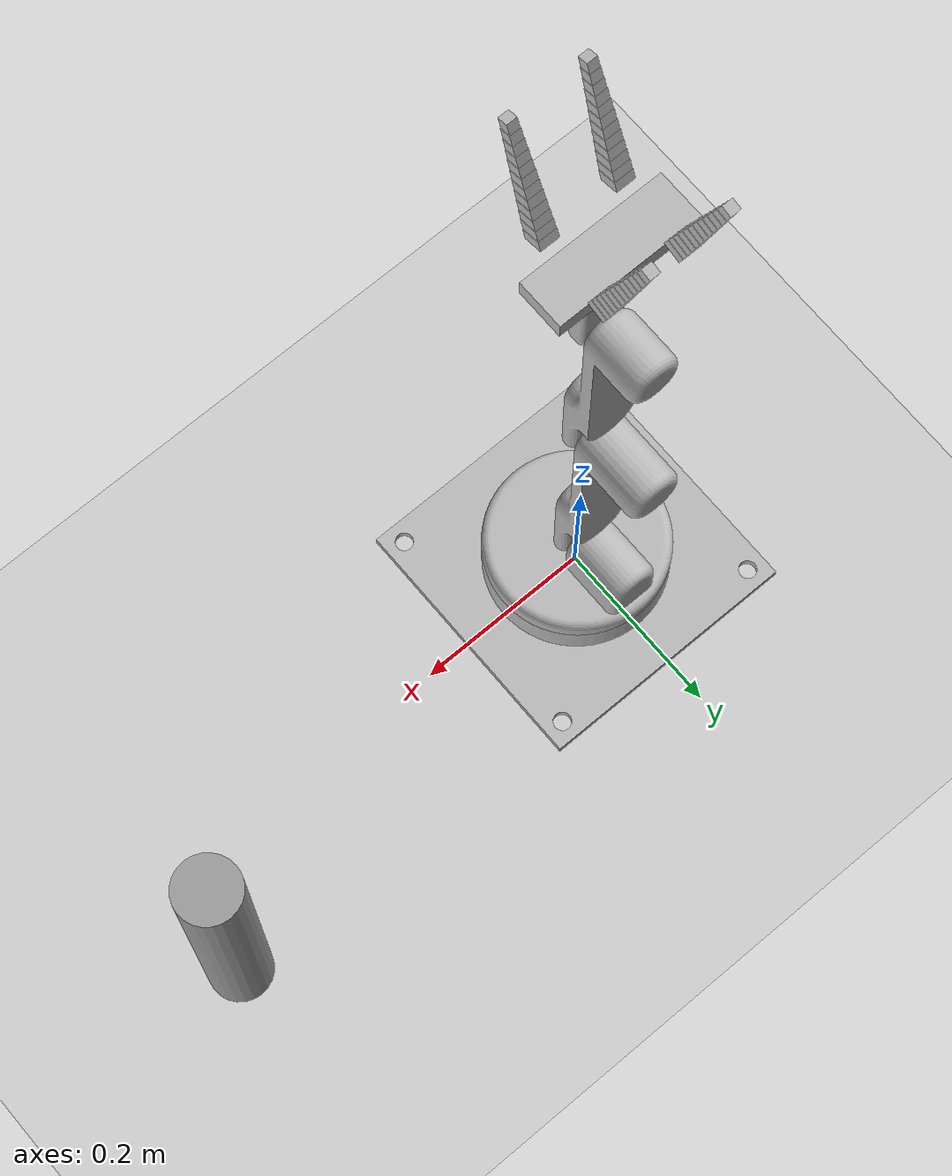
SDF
<sdf version="1.6">
 <world name="default">
  <light name="sun" type="directional">
   <pose>0 0 10 0 -0 0</pose>
   <diffuse>0.8 0.8 0.8 1</diffuse>
   <specular>0.2 0.2 0.2 1</specular>
   <attenuation>
    <range>1000</range>
    <constant>0.9</constant>
    <linear>0.01</linear>
    <quadratic>0.001</quadratic>
   </attenuation>
   <direction>-0.5 0.1 -0.9</direction>
  </light>
  <model name="ground_plane">
   <static>1</static>
   <link name="link">
    <collision name="collision">
     <geometry><plane><normal>0 0 1</normal><size>100 100</size></plane></geometry>
     <surface>
      <contact><collide_bitmask>65535</collide_bitmask></contact>
      <friction><ode><mu>100</mu><mu2>50</mu2></ode></friction>
     </surface>
    </collision>
    <visual name="visual">
     <cast_shadows>0</cast_shadows>
     <geometry><plane><normal>0 0 1</normal><size>100 100</size></plane></geometry>
     <material>
      <script><uri>file://media/materials/scripts/gazebo.material</uri><name>Gazebo/Grey</name></script>
     </material>
    </visual>
   </link>
  </model>
  <gravity>0 0 -9.8</gravity>
  <magnetic_field>6e-06 2.3e-05 -4.2e-05</magnetic_field>
  <atmosphere type="adiabatic"/>
  <physics name="default_physics" default="0" type="ode">
   <max_step_size>0.001</max_step_size>
   <real_time_factor>1</real_time_factor>
   <real_time_update_rate>1000</real_time_update_rate>
  </physics>
  <scene><ambient>0.4 0.4 0.4 1</ambient><background>0.7 0.7 0.7 1</background><shadows>1</shadows></scene>
  <audio><device>default</device></audio>
  <spherical_coordinates>
   <surface_model>EARTH_WGS84</surface_model>
   <latitude_deg>0</latitude_deg>
   <longitude_deg>0</longitude_deg>
   <elevation>0</elevation>
   <heading_deg>0</heading_deg>
  </spherical_coordinates>
  <model name="Design">
   <link name="base_link">
    <inertial>
     <pose>-0 0 0.019653 0 -0 0</pose>
     <mass>16.831</mass>
     <inertia>
      <ixx>0.079936</ixx>
      <ixy>0</ixy>
      <ixz>-0</ixz>
      <iyy>0.079936</iyy>
      <iyz>0</iyz>
      <izz>0.152021</izz>
     </inertia>
    </inertial>
    <collision name="base_link_collision">
     <geometry>
      <mesh>
       <scale>0.001 0.001 0.001</scale>
       <uri>/home/ben/catkin_ws/src/Soft-Arm-Main/meshes/base_link.stl</uri>
      </mesh>
     </geometry>
    </collision>
    <visual name="base_link_visual">
     <geometry>
      <mesh>
       <scale>0.001 0.001 0.001</scale>
       <uri>/home/ben/catkin_ws/src/Soft-Arm-Main/meshes/base_link.stl</uri>
      </mesh>
     </geometry>
    </visual>
   </link>
   <joint name="world_joint" type="fixed"><child>base_link</child><parent>world</parent></joint>
   <link name="Link1_1">
    <pose>0 0 0.05 0 -0 0</pose>
    <inertial>
     <pose>-1.2e-05 0.014425 0.020603 0 -0 0</pose>
     <mass>0.917871</mass>
     <inertia>
      <ixx>0.002553</ixx>
      <ixy>0</ixy>
      <ixz>0</ixz>
      <iyy>0.002018</iyy>
      <iyz>-0.00035</iyz>
      <izz>0.00387</izz>
     </inertia>
    </inertial>
    <collision name="Link1_1_collision">
     <pose>-0 -0 -0.05 0 -0 0</pose>
     <geometry>
      <mesh>
       <scale>0.001 0.001 0.001</scale>
       <uri>/home/ben/catkin_ws/src/Soft-Arm-Main/meshes/Link1_1.stl</uri>
      </mesh>
     </geometry>
    </collision>
    <visual name="Link1_1_visual">
     <pose>-0 -0 -0.05 0 -0 0</pose>
     <geometry>
      <mesh>
       <scale>0.001 0.001 0.001</scale>
       <uri>/home/ben/catkin_ws/src/Soft-Arm-Main/meshes/Link1_1.stl</uri>
      </mesh>
     </geometry>
    </visual>
   </link>
   <joint name="Rev1" type="revolute">
    <child>Link1_1</child>
    <parent>base_link</parent>
    <axis>
     <xyz>0 0 1</xyz>
     <limit><lower>-1e+16</lower><upper>1e+16</upper></limit>
     <dynamics>
      <damping>0</damping>
      <friction>0</friction>
      <spring_reference>0</spring_reference>
      <spring_stiffness>0</spring_stiffness>
     </dynamics>
     <use_parent_model_frame>1</use_parent_model_frame>
    </axis>
   </joint>
   <link name="Link2_1">
    <pose>-4.2e-05 0.009807 0.1 0 -0 0</pose>
    <inertial>
     <pose>-0 0.018054 0.186857 0 -0 0</pose>
     <mass>0.712051</mass>
     <inertia>
      <ixx>0.008737</ixx>
      <ixy>0</ixy>
      <ixz>0</ixz>
      <iyy>0.008392</iyy>
      <iyz>-0.001509</iyz>
      <izz>0.000705</izz>
     </inertia>
    </inertial>
    <collision name="Link2_1_collision">
     <pose>4.2e-05 -0.009807 -0.1 0 -0 0</pose>
     <geometry>
      <mesh>
       <scale>0.001 0.001 0.001</scale>
       <uri>/home/ben/catkin_ws/src/Soft-Arm-Main/meshes/Link2_1.stl</uri>
      </mesh>
     </geometry>
    </collision>
    <visual name="Link2_1_visual">
     <pose>4.2e-05 -0.009807 -0.1 0 -0 0</pose>
     <geometry>
      <mesh>
       <scale>0.001 0.001 0.001</scale>
       <uri>/home/ben/catkin_ws/src/Soft-Arm-Main/meshes/Link2_1.stl</uri>
      </mesh>
     </geometry>
    </visual>
   </link>
   <joint name="Rev2" type="revolute">
    <child>Link2_1</child>
    <parent>Link1_1</parent>
    <axis>
     <xyz>0 -1 0</xyz>
     <limit><lower>-1.39626</lower><upper>1.39626</upper><effort>10000</effort><velocity>0.01</velocity></limit>
     <dynamics>
      <damping>0</damping>
      <friction>0</friction>
      <spring_reference>0</spring_reference>
      <spring_stiffness>0</spring_stiffness>
     </dynamics>
     <use_parent_model_frame>1</use_parent_model_frame>
    </axis>
   </joint>
   <link name="Link3_1">
    <pose>-4.2e-05 0.009807 0.4 0 -0 0</pose>
    <inertial>
     <pose>3.9e-05 0.012744 0.14887 0 -0 0</pose>
     <mass>0.535296</mass>
     <inertia>
      <ixx>0.004471</ixx>
      <ixy>-0</ixy>
      <ixz>-1e-06</ixz>
      <iyy>0.004348</iyy>
      <iyz>-0.000747</iyz>
      <izz>0.000361</izz>
     </inertia>
    </inertial>
    <collision name="Link3_1_collision">
     <pose>4.2e-05 -0.009807 -0.4 0 -0 0</pose>
     <geometry>
      <mesh>
       <scale>0.001 0.001 0.001</scale>
       <uri>/home/ben/catkin_ws/src/Soft-Arm-Main/meshes/Link3_1.stl</uri>
      </mesh>
     </geometry>
    </collision>
    <visual name="Link3_1_visual">
     <pose>4.2e-05 -0.009807 -0.4 0 -0 0</pose>
     <geometry>
      <mesh>
       <scale>0.001 0.001 0.001</scale>
       <uri>/home/ben/catkin_ws/src/Soft-Arm-Main/meshes/Link3_1.stl</uri>
      </mesh>
     </geometry>
    </visual>
   </link>
   <joint name="Rev3" type="revolute">
    <child>Link3_1</child>
    <parent>Link2_1</parent>
    <axis>
     <xyz>0 -1 0</xyz>
     <limit><lower>-2.79253</lower><upper>2.79253</upper><effort>10000</effort><velocity>0.01</velocity></limit>
     <dynamics>
      <damping>0</damping>
      <friction>0</friction>
      <spring_reference>0</spring_reference>
      <spring_stiffness>0</spring_stiffness>
     </dynamics>
     <use_parent_model_frame>1</use_parent_model_frame>
    </axis>
   </joint>
   <link name="Link4_1">
    <pose>2.4e-05 0.009807 0.65 0 -0 0</pose>
    <inertial>
     <pose>-0 -0.00645 0.095158 0 -0 0</pose>
     <mass>0.281689</mass>
     <inertia>
      <ixx>0.00191875</ixx>
      <ixy>0.001</ixy>
      <ixz>0.000999998</ixz>
      <iyy>0.0019433</iyy>
      <iyz>0.000945156</iyz>
      <izz>0.00104945</izz>
     </inertia>
    </inertial>
    <collision name="Link4_1_collision">
     <pose>-2.4e-05 -0.009807 -0.65 0 -0 0</pose>
     <geometry>
      <mesh>
       <scale>0.001 0.001 0.001</scale>
       <uri>/home/ben/catkin_ws/src/Soft-Arm-Main/meshes/Link4_1.stl</uri>
      </mesh>
     </geometry>
    </collision>
    <collision name="Link4_1_fixed_joint_lump__palm_collision_1">
     <pose>0 0 0.15 0 -0 0</pose>
     <geometry><box><size>0.15 0.05 0.02</size></box></geometry>
     <surface><friction><ode><mu>2000</mu><mu2>2000</mu2></ode></friction></surface>
    </collision>
    <visual name="Link4_1_visual">
     <pose>-2.4e-05 -0.009807 -0.65 0 -0 0</pose>
     <geometry>
      <mesh>
       <scale>0.001 0.001 0.001</scale>
       <uri>/home/ben/catkin_ws/src/Soft-Arm-Main/meshes/Link4_1.stl</uri>
      </mesh>
     </geometry>
    </visual>
    <visual name="Link4_1_fixed_joint_lump__palm_visual_1">
     <pose>0 0 0.15 0 -0 0</pose>
     <geometry><box><size>0.15 0.05 0.02</size></box></geometry>
     <material><script><uri>__default__</uri><name>__default__</name></script></material>
    </visual>
    <self_collide>1</self_collide>
   </link>
   <joint name="Rev4" type="revolute">
    <child>Link4_1</child>
    <parent>Link3_1</parent>
    <axis>
     <xyz>0 -1 0</xyz>
     <limit><lower>-2.61799</lower><upper>2.61799</upper><effort>10000</effort><velocity>0.01</velocity></limit>
     <dynamics>
      <damping>0</damping>
      <friction>0</friction>
      <spring_reference>0</spring_reference>
      <spring_stiffness>0</spring_stiffness>
     </dynamics>
     <use_parent_model_frame>1</use_parent_model_frame>
    </axis>
   </joint>
   <link name="LBseg1">
    <pose>-0.039976 0.049807 0.83 -0.3 0 0</pose>
    <inertial>
     <mass>0.01</mass>
     <inertia>
      <ixx>4.63541e-07</ixx>
      <ixy>0</ixy>
      <ixz>0</ixz>
      <iyy>4.63541e-07</iyy>
      <iyz>0</iyz>
      <izz>6.66666e-07</izz>
     </inertia>
    </inertial>
    <collision name="LBseg1_collision_collision">
     <geometry><box><size>0.02 0.02 0.0125</size></box></geometry>
     <surface><friction><ode><mu>20000</mu><mu2>20000</mu2></ode></friction></surface>
    </collision>
    <visual name="LBseg1_visual">
     <geometry><box><size>0.02 0.02 0.0125</size></box></geometry>
     <material><script><uri>__default__</uri><name>__default__</name></script></material>
    </visual>
    <self_collide>1</self_collide>
    <sensor name="LBseg1_sensor" type="contact">
     <always_on>1</always_on>
     <contact><collision>LBseg1_collision</collision><topic>__default_topic__</topic></contact>
     <update_rate>30</update_rate>
    </sensor>
   </link>
   <joint name="palm_LBseg1_joint" type="revolute">
    <child>LBseg1</child>
    <parent>Link4_1</parent>
    <axis>
     <xyz>1 0 0</xyz>
     <limit><lower>-0</lower><upper>0</upper><effort>2</effort><velocity>0.0001</velocity></limit>
     <dynamics><spring_reference>0</spring_reference><spring_stiffness>0</spring_stiffness></dynamics>
     <use_parent_model_frame>1</use_parent_model_frame>
    </axis>
    <physics><ode><limit><cfm>0</cfm><erp>0.2</erp></limit></ode></physics>
   </joint>
   <link name="LBseg2">
    <pose>-0.039976 0.053501 0.841942 -0.3 0 0</pose>
    <inertial>
     <mass>0.01</mass>
     <inertia>
      <ixx>4.36342e-07</ixx>
      <ixy>0</ixy>
      <ixz>0</ixz>
      <iyy>4.36342e-07</iyy>
      <iyz>0</iyz>
      <izz>6.12268e-07</izz>
     </inertia>
    </inertial>
    <collision name="LBseg2_collision_collision">
     <geometry><box><size>0.019167 0.019167 0.0125</size></box></geometry>
     <surface><friction><ode><mu>20000</mu><mu2>20000</mu2></ode></friction></surface>
    </collision>
    <visual name="LBseg2_visual">
     <geometry><box><size>0.019167 0.019167 0.0125</size></box></geometry>
     <material><script><uri>__default__</uri><name>__default__</name></script></material>
    </visual>
    <self_collide>1</self_collide>
    <sensor name="LBseg2_sensor" type="contact">
     <always_on>1</always_on>
     <contact><collision>LBseg2_collision</collision><topic>__default_topic__</topic></contact>
     <update_rate>30</update_rate>
    </sensor>
   </link>
   <joint name="LBseg1_LBseg2_joint" type="revolute">
    <child>LBseg2</child>
    <parent>LBseg1</parent>
    <axis>
     <xyz>1 0 0</xyz>
     <limit><lower>-2</lower><upper>2</upper><effort>2</effort><velocity>0.001</velocity></limit>
     <dynamics>
      <damping>0.02</damping>
      <friction>0</friction>
      <spring_reference>0</spring_reference>
      <spring_stiffness>0</spring_stiffness>
     </dynamics>
     <use_parent_model_frame>1</use_parent_model_frame>
    </axis>
    <physics>
     <ode>
      <implicit_spring_damper>1</implicit_spring_damper>
      <cfm_damping>1</cfm_damping>
      <limit><cfm>0</cfm><erp>0.2</erp></limit>
     </ode>
    </physics>
   </joint>
   <link name="LBseg3">
    <pose>-0.039976 0.057195 0.853883 -0.3 0 0</pose>
    <inertial>
     <mass>0.01</mass>
     <inertia>
      <ixx>4.10301e-07</ixx>
      <ixy>0</ixy>
      <ixz>0</ixz>
      <iyy>4.10301e-07</iyy>
      <iyz>0</iyz>
      <izz>5.60185e-07</izz>
     </inertia>
    </inertial>
    <collision name="LBseg3_collision_collision">
     <geometry><box><size>0.018333 0.018333 0.0125</size></box></geometry>
     <surface><friction><ode><mu>20000</mu><mu2>20000</mu2></ode></friction></surface>
    </collision>
    <visual name="LBseg3_visual">
     <geometry><box><size>0.018333 0.018333 0.0125</size></box></geometry>
     <material><script><uri>__default__</uri><name>__default__</name></script></material>
    </visual>
    <self_collide>1</self_collide>
    <sensor name="LBseg3_sensor" type="contact">
     <always_on>1</always_on>
     <contact><collision>LBseg3_collision</collision><topic>__default_topic__</topic></contact>
     <update_rate>30</update_rate>
    </sensor>
   </link>
   <joint name="LBseg2_LBseg3_joint" type="revolute">
    <child>LBseg3</child>
    <parent>LBseg2</parent>
    <axis>
     <xyz>1 0 0</xyz>
     <limit><lower>-2</lower><upper>2</upper><effort>2</effort><velocity>0.001</velocity></limit>
     <dynamics>
      <damping>0.02</damping>
      <friction>0</friction>
      <spring_reference>0</spring_reference>
      <spring_stiffness>0</spring_stiffness>
     </dynamics>
     <use_parent_model_frame>1</use_parent_model_frame>
    </axis>
    <physics>
     <ode>
      <implicit_spring_damper>1</implicit_spring_damper>
      <cfm_damping>1</cfm_damping>
      <limit><cfm>0</cfm><erp>0.2</erp></limit>
     </ode>
    </physics>
   </joint>
   <link name="LBseg4">
    <pose>-0.039976 0.060889 0.865825 -0.3 0 0</pose>
    <inertial>
     <mass>0.01</mass>
     <inertia>
      <ixx>3.85417e-07</ixx>
      <ixy>0</ixy>
      <ixz>0</ixz>
      <iyy>3.85417e-07</iyy>
      <iyz>0</iyz>
      <izz>5.10416e-07</izz>
     </inertia>
    </inertial>
    <collision name="LBseg4_collision_collision">
     <geometry><box><size>0.0175 0.0175 0.0125</size></box></geometry>
     <surface><friction><ode><mu>20000</mu><mu2>20000</mu2></ode></friction></surface>
    </collision>
    <visual name="LBseg4_visual">
     <geometry><box><size>0.0175 0.0175 0.0125</size></box></geometry>
     <material><script><uri>__default__</uri><name>__default__</name></script></material>
    </visual>
    <self_collide>1</self_collide>
    <sensor name="LBseg4_sensor" type="contact">
     <always_on>1</always_on>
     <contact><collision>LBseg4_collision</collision><topic>__default_topic__</topic></contact>
     <update_rate>30</update_rate>
    </sensor>
   </link>
   <joint name="LBseg3_LBseg4_joint" type="revolute">
    <child>LBseg4</child>
    <parent>LBseg3</parent>
    <axis>
     <xyz>1 0 0</xyz>
     <limit><lower>-2</lower><upper>2</upper><effort>2</effort><velocity>0.001</velocity></limit>
     <dynamics>
      <damping>0.02</damping>
      <friction>0</friction>
      <spring_reference>0</spring_reference>
      <spring_stiffness>0</spring_stiffness>
     </dynamics>
     <use_parent_model_frame>1</use_parent_model_frame>
    </axis>
    <physics>
     <ode>
      <implicit_spring_damper>1</implicit_spring_damper>
      <cfm_damping>1</cfm_damping>
      <limit><cfm>0</cfm><erp>0.2</erp></limit>
     </ode>
    </physics>
   </joint>
   <link name="LBseg5">
    <pose>-0.039976 0.064583 0.877767 -0.3 0 0</pose>
    <inertial>
     <mass>0.01</mass>
     <inertia>
      <ixx>3.6169e-07</ixx>
      <ixy>0</ixy>
      <ixz>0</ixz>
      <iyy>3.6169e-07</iyy>
      <iyz>0</iyz>
      <izz>4.62963e-07</izz>
     </inertia>
    </inertial>
    <collision name="LBseg5_collision_collision">
     <geometry><box><size>0.016667 0.016667 0.0125</size></box></geometry>
     <surface><friction><ode><mu>20000</mu><mu2>20000</mu2></ode></friction></surface>
    </collision>
    <visual name="LBseg5_visual">
     <geometry><box><size>0.016667 0.016667 0.0125</size></box></geometry>
     <material><script><uri>__default__</uri><name>__default__</name></script></material>
    </visual>
    <self_collide>1</self_collide>
    <sensor name="LBseg5_sensor" type="contact">
     <always_on>1</always_on>
     <contact><collision>LBseg5_collision</collision><topic>__default_topic__</topic></contact>
     <update_rate>30</update_rate>
    </sensor>
   </link>
   <joint name="LBseg4_LBseg5_joint" type="revolute">
    <child>LBseg5</child>
    <parent>LBseg4</parent>
    <axis>
     <xyz>1 0 0</xyz>
     <limit><lower>-2</lower><upper>2</upper><effort>2</effort><velocity>0.001</velocity></limit>
     <dynamics>
      <damping>0.02</damping>
      <friction>0</friction>
      <spring_reference>0</spring_reference>
      <spring_stiffness>0</spring_stiffness>
     </dynamics>
     <use_parent_model_frame>1</use_parent_model_frame>
    </axis>
    <physics>
     <ode>
      <implicit_spring_damper>1</implicit_spring_damper>
      <cfm_damping>1</cfm_damping>
      <limit><cfm>0</cfm><erp>0.2</erp></limit>
     </ode>
    </physics>
   </joint>
   <link name="LBseg6">
    <pose>-0.039976 0.068277 0.889709 -0.3 0 0</pose>
    <inertial>
     <mass>0.01</mass>
     <inertia>
      <ixx>3.3912e-07</ixx>
      <ixy>0</ixy>
      <ixz>0</ixz>
      <iyy>3.3912e-07</iyy>
      <iyz>0</iyz>
      <izz>4.17824e-07</izz>
     </inertia>
    </inertial>
    <collision name="LBseg6_collision_collision">
     <geometry><box><size>0.015833 0.015833 0.0125</size></box></geometry>
     <surface><friction><ode><mu>20000</mu><mu2>20000</mu2></ode></friction></surface>
    </collision>
    <visual name="LBseg6_visual">
     <geometry><box><size>0.015833 0.015833 0.0125</size></box></geometry>
     <material><script><uri>__default__</uri><name>__default__</name></script></material>
    </visual>
    <self_collide>1</self_collide>
    <sensor name="LBseg6_sensor" type="contact">
     <always_on>1</always_on>
     <contact><collision>LBseg6_collision</collision><topic>__default_topic__</topic></contact>
     <update_rate>30</update_rate>
    </sensor>
   </link>
   <joint name="LBseg5_LBseg6_joint" type="revolute">
    <child>LBseg6</child>
    <parent>LBseg5</parent>
    <axis>
     <xyz>1 0 0</xyz>
     <limit><lower>-2</lower><upper>2</upper><effort>2</effort><velocity>0.001</velocity></limit>
     <dynamics>
      <damping>0.02</damping>
      <friction>0</friction>
      <spring_reference>0</spring_reference>
      <spring_stiffness>0</spring_stiffness>
     </dynamics>
     <use_parent_model_frame>1</use_parent_model_frame>
    </axis>
    <physics>
     <ode>
      <implicit_spring_damper>1</implicit_spring_damper>
      <cfm_damping>1</cfm_damping>
      <limit><cfm>0</cfm><erp>0.2</erp></limit>
     </ode>
    </physics>
   </joint>
   <link name="LBseg7">
    <pose>-0.039976 0.071971 0.90165 -0.3 0 0</pose>
    <inertial>
     <mass>0.01</mass>
     <inertia>
      <ixx>3.17708e-07</ixx>
      <ixy>0</ixy>
      <ixz>0</ixz>
      <iyy>3.17708e-07</iyy>
      <iyz>0</iyz>
      <izz>3.75e-07</izz>
     </inertia>
    </inertial>
    <collision name="LBseg7_collision_collision">
     <geometry><box><size>0.015 0.015 0.0125</size></box></geometry>
     <surface><friction><ode><mu>20000</mu><mu2>20000</mu2></ode></friction></surface>
    </collision>
    <visual name="LBseg7_visual">
     <geometry><box><size>0.015 0.015 0.0125</size></box></geometry>
     <material><script><uri>__default__</uri><name>__default__</name></script></material>
    </visual>
    <self_collide>1</self_collide>
    <sensor name="LBseg7_sensor" type="contact">
     <always_on>1</always_on>
     <contact><collision>LBseg7_collision</collision><topic>__default_topic__</topic></contact>
     <update_rate>30</update_rate>
    </sensor>
   </link>
   <joint name="LBseg6_LBseg7_joint" type="revolute">
    <child>LBseg7</child>
    <parent>LBseg6</parent>
    <axis>
     <xyz>1 0 0</xyz>
     <limit><lower>-2</lower><upper>2</upper><effort>2</effort><velocity>0.001</velocity></limit>
     <dynamics>
      <damping>0.02</damping>
      <friction>0</friction>
      <spring_reference>0</spring_reference>
      <spring_stiffness>0</spring_stiffness>
     </dynamics>
     <use_parent_model_frame>1</use_parent_model_frame>
    </axis>
    <physics>
     <ode>
      <implicit_spring_damper>1</implicit_spring_damper>
      <cfm_damping>1</cfm_damping>
      <limit><cfm>0</cfm><erp>0.2</erp></limit>
     </ode>
    </physics>
   </joint>
   <link name="LBseg8">
    <pose>-0.039976 0.075665 0.913592 -0.3 0 0</pose>
    <inertial>
     <mass>0.01</mass>
     <inertia>
      <ixx>2.97454e-07</ixx>
      <ixy>0</ixy>
      <ixz>0</ixz>
      <iyy>2.97454e-07</iyy>
      <iyz>0</iyz>
      <izz>3.34491e-07</izz>
     </inertia>
    </inertial>
    <collision name="LBseg8_collision_collision">
     <geometry><box><size>0.014167 0.014167 0.0125</size></box></geometry>
     <surface><friction><ode><mu>20000</mu><mu2>20000</mu2></ode></friction></surface>
    </collision>
    <visual name="LBseg8_visual">
     <geometry><box><size>0.014167 0.014167 0.0125</size></box></geometry>
     <material><script><uri>__default__</uri><name>__default__</name></script></material>
    </visual>
    <self_collide>1</self_collide>
    <sensor name="LBseg8_sensor" type="contact">
     <always_on>1</always_on>
     <contact><collision>LBseg8_collision</collision><topic>__default_topic__</topic></contact>
     <update_rate>30</update_rate>
    </sensor>
   </link>
   <joint name="LBseg7_LBseg8_joint" type="revolute">
    <child>LBseg8</child>
    <parent>LBseg7</parent>
    <axis>
     <xyz>1 0 0</xyz>
     <limit><lower>-2</lower><upper>2</upper><effort>2</effort><velocity>0.001</velocity></limit>
     <dynamics>
      <damping>0.02</damping>
      <friction>0</friction>
      <spring_reference>0</spring_reference>
      <spring_stiffness>0</spring_stiffness>
     </dynamics>
     <use_parent_model_frame>1</use_parent_model_frame>
    </axis>
    <physics>
     <ode>
      <implicit_spring_damper>1</implicit_spring_damper>
      <cfm_damping>1</cfm_damping>
      <limit><cfm>0</cfm><erp>0.2</erp></limit>
     </ode>
    </physics>
   </joint>
   <link name="LBseg9">
    <pose>-0.039976 0.079359 0.925534 -0.3 0 0</pose>
    <inertial>
     <mass>0.01</mass>
     <inertia>
      <ixx>2.78356e-07</ixx>
      <ixy>0</ixy>
      <ixz>0</ixz>
      <iyy>2.78356e-07</iyy>
      <iyz>0</iyz>
      <izz>2.96296e-07</izz>
     </inertia>
    </inertial>
    <collision name="LBseg9_collision_collision">
     <geometry><box><size>0.013333 0.013333 0.0125</size></box></geometry>
     <surface><friction><ode><mu>20000</mu><mu2>20000</mu2></ode></friction></surface>
    </collision>
    <visual name="LBseg9_visual">
     <geometry><box><size>0.013333 0.013333 0.0125</size></box></geometry>
     <material><script><uri>__default__</uri><name>__default__</name></script></material>
    </visual>
    <self_collide>1</self_collide>
    <sensor name="LBseg9_sensor" type="contact">
     <always_on>1</always_on>
     <contact><collision>LBseg9_collision</collision><topic>__default_topic__</topic></contact>
     <update_rate>30</update_rate>
    </sensor>
   </link>
   <joint name="LBseg8_LBseg9_joint" type="revolute">
    <child>LBseg9</child>
    <parent>LBseg8</parent>
    <axis>
     <xyz>1 0 0</xyz>
     <limit><lower>-2</lower><upper>2</upper><effort>2</effort><velocity>0.001</velocity></limit>
     <dynamics>
      <damping>0.02</damping>
      <friction>0</friction>
      <spring_reference>0</spring_reference>
      <spring_stiffness>0</spring_stiffness>
     </dynamics>
     <use_parent_model_frame>1</use_parent_model_frame>
    </axis>
    <physics>
     <ode>
      <implicit_spring_damper>1</implicit_spring_damper>
      <cfm_damping>1</cfm_damping>
      <limit><cfm>0</cfm><erp>0.2</erp></limit>
     </ode>
    </physics>
   </joint>
   <link name="LBseg10">
    <pose>-0.039976 0.083053 0.937475 -0.3 0 0</pose>
    <inertial>
     <mass>0.01</mass>
     <inertia>
      <ixx>2.60417e-07</ixx>
      <ixy>0</ixy>
      <ixz>0</ixz>
      <iyy>2.60417e-07</iyy>
      <iyz>0</iyz>
      <izz>2.60417e-07</izz>
     </inertia>
    </inertial>
    <collision name="LBseg10_collision_collision">
     <geometry><box><size>0.0125 0.0125 0.0125</size></box></geometry>
     <surface><friction><ode><mu>20000</mu><mu2>20000</mu2></ode></friction></surface>
    </collision>
    <visual name="LBseg10_visual">
     <geometry><box><size>0.0125 0.0125 0.0125</size></box></geometry>
     <material><script><uri>__default__</uri><name>__default__</name></script></material>
    </visual>
    <self_collide>1</self_collide>
    <sensor name="LBseg10_sensor" type="contact">
     <always_on>1</always_on>
     <contact><collision>LBseg10_collision</collision><topic>__default_topic__</topic></contact>
     <update_rate>30</update_rate>
    </sensor>
   </link>
   <joint name="LBseg9_LBseg10_joint" type="revolute">
    <child>LBseg10</child>
    <parent>LBseg9</parent>
    <axis>
     <xyz>1 0 0</xyz>
     <limit><lower>-2</lower><upper>2</upper><effort>2</effort><velocity>0.001</velocity></limit>
     <dynamics>
      <damping>0.02</damping>
      <friction>0</friction>
      <spring_reference>0</spring_reference>
      <spring_stiffness>0</spring_stiffness>
     </dynamics>
     <use_parent_model_frame>1</use_parent_model_frame>
    </axis>
    <physics>
     <ode>
      <implicit_spring_damper>1</implicit_spring_damper>
      <cfm_damping>1</cfm_damping>
      <limit><cfm>0</cfm><erp>0.2</erp></limit>
     </ode>
    </physics>
   </joint>
   <link name="LBseg11">
    <pose>-0.039976 0.086747 0.949417 -0.3 0 0</pose>
    <inertial>
     <mass>0.01</mass>
     <inertia>
      <ixx>2.43634e-07</ixx>
      <ixy>0</ixy>
      <ixz>0</ixz>
      <iyy>2.43634e-07</iyy>
      <iyz>0</iyz>
      <izz>2.26852e-07</izz>
     </inertia>
    </inertial>
    <collision name="LBseg11_collision_collision">
     <geometry><box><size>0.011667 0.011667 0.0125</size></box></geometry>
     <surface><friction><ode><mu>20000</mu><mu2>20000</mu2></ode></friction></surface>
    </collision>
    <visual name="LBseg11_visual">
     <geometry><box><size>0.011667 0.011667 0.0125</size></box></geometry>
     <material><script><uri>__default__</uri><name>__default__</name></script></material>
    </visual>
    <self_collide>1</self_collide>
    <sensor name="LBseg11_sensor" type="contact">
     <always_on>1</always_on>
     <contact><collision>LBseg11_collision</collision><topic>__default_topic__</topic></contact>
     <update_rate>30</update_rate>
    </sensor>
   </link>
   <joint name="LBseg10_LBseg11_joint" type="revolute">
    <child>LBseg11</child>
    <parent>LBseg10</parent>
    <axis>
     <xyz>1 0 0</xyz>
     <limit><lower>-2</lower><upper>2</upper><effort>2</effort><velocity>0.001</velocity></limit>
     <dynamics>
      <damping>0.02</damping>
      <friction>0</friction>
      <spring_reference>0</spring_reference>
      <spring_stiffness>0</spring_stiffness>
     </dynamics>
     <use_parent_model_frame>1</use_parent_model_frame>
    </axis>
    <physics>
     <ode>
      <implicit_spring_damper>1</implicit_spring_damper>
      <cfm_damping>1</cfm_damping>
      <limit><cfm>0</cfm><erp>0.2</erp></limit>
     </ode>
    </physics>
   </joint>
   <link name="LBseg12">
    <pose>-0.039976 0.090441 0.961359 -0.3 0 0</pose>
    <inertial>
     <mass>0.01</mass>
     <inertia>
      <ixx>2.28009e-07</ixx>
      <ixy>0</ixy>
      <ixz>0</ixz>
      <iyy>2.28009e-07</iyy>
      <iyz>0</iyz>
      <izz>1.95602e-07</izz>
     </inertia>
    </inertial>
    <collision name="LBseg12_collision_collision">
     <geometry><box><size>0.010833 0.010833 0.0125</size></box></geometry>
     <surface><friction><ode><mu>20000</mu><mu2>20000</mu2></ode></friction></surface>
    </collision>
    <visual name="LBseg12_visual">
     <geometry><box><size>0.010833 0.010833 0.0125</size></box></geometry>
     <material><script><uri>__default__</uri><name>__default__</name></script></material>
    </visual>
    <self_collide>1</self_collide>
    <sensor name="LBseg12_sensor" type="contact">
     <always_on>1</always_on>
     <contact><collision>LBseg12_collision</collision><topic>__default_topic__</topic></contact>
     <update_rate>30</update_rate>
    </sensor>
   </link>
   <joint name="LBseg11_LBseg12_joint" type="revolute">
    <child>LBseg12</child>
    <parent>LBseg11</parent>
    <axis>
     <xyz>1 0 0</xyz>
     <limit><lower>-2</lower><upper>2</upper><effort>2</effort><velocity>0.001</velocity></limit>
     <dynamics>
      <damping>0.02</damping>
      <friction>0</friction>
      <spring_reference>0</spring_reference>
      <spring_stiffness>0</spring_stiffness>
     </dynamics>
     <use_parent_model_frame>1</use_parent_model_frame>
    </axis>
    <physics>
     <ode>
      <implicit_spring_damper>1</implicit_spring_damper>
      <cfm_damping>1</cfm_damping>
      <limit><cfm>0</cfm><erp>0.2</erp></limit>
     </ode>
    </physics>
   </joint>
   <link name="LTseg1">
    <pose>0.040024 0.049807 0.83 -0.3 0 0</pose>
    <inertial>
     <mass>0.01</mass>
     <inertia>
      <ixx>4.63541e-07</ixx>
      <ixy>0</ixy>
      <ixz>0</ixz>
      <iyy>4.63541e-07</iyy>
      <iyz>0</iyz>
      <izz>6.66666e-07</izz>
     </inertia>
    </inertial>
    <collision name="LTseg1_collision_collision">
     <geometry><box><size>0.02 0.02 0.0125</size></box></geometry>
     <surface><friction><ode><mu>20000</mu><mu2>20000</mu2></ode></friction></surface>
    </collision>
    <visual name="LTseg1_visual">
     <geometry><box><size>0.02 0.02 0.0125</size></box></geometry>
     <material><script><uri>__default__</uri><name>__default__</name></script></material>
    </visual>
    <self_collide>1</self_collide>
    <sensor name="LTseg1_sensor" type="contact">
     <always_on>1</always_on>
     <contact><collision>LTseg1_collision</collision><topic>__default_topic__</topic></contact>
     <update_rate>30</update_rate>
    </sensor>
   </link>
   <joint name="palm_LTseg1_joint" type="revolute">
    <child>LTseg1</child>
    <parent>Link4_1</parent>
    <axis>
     <xyz>1 0 0</xyz>
     <limit><lower>-0</lower><upper>0</upper><effort>2</effort><velocity>0.0001</velocity></limit>
     <dynamics><spring_reference>0</spring_reference><spring_stiffness>0</spring_stiffness></dynamics>
     <use_parent_model_frame>1</use_parent_model_frame>
    </axis>
    <physics><ode><limit><cfm>0</cfm><erp>0.2</erp></limit></ode></physics>
   </joint>
   <link name="LTseg2">
    <pose>0.040024 0.053501 0.841942 -0.3 0 0</pose>
    <inertial>
     <mass>0.01</mass>
     <inertia>
      <ixx>4.36342e-07</ixx>
      <ixy>0</ixy>
      <ixz>0</ixz>
      <iyy>4.36342e-07</iyy>
      <iyz>0</iyz>
      <izz>6.12268e-07</izz>
     </inertia>
    </inertial>
    <collision name="LTseg2_collision_collision">
     <geometry><box><size>0.019167 0.019167 0.0125</size></box></geometry>
     <surface><friction><ode><mu>20000</mu><mu2>20000</mu2></ode></friction></surface>
    </collision>
    <visual name="LTseg2_visual">
     <geometry><box><size>0.019167 0.019167 0.0125</size></box></geometry>
     <material><script><uri>__default__</uri><name>__default__</name></script></material>
    </visual>
    <self_collide>1</self_collide>
    <sensor name="LTseg2_sensor" type="contact">
     <always_on>1</always_on>
     <contact><collision>LTseg2_collision</collision><topic>__default_topic__</topic></contact>
     <update_rate>30</update_rate>
    </sensor>
   </link>
   <joint name="LTseg1_LTseg2_joint" type="revolute">
    <child>LTseg2</child>
    <parent>LTseg1</parent>
    <axis>
     <xyz>1 0 0</xyz>
     <limit><lower>-2</lower><upper>2</upper><effort>2</effort><velocity>0.001</velocity></limit>
     <dynamics>
      <damping>0.02</damping>
      <friction>0</friction>
      <spring_reference>0</spring_reference>
      <spring_stiffness>0</spring_stiffness>
     </dynamics>
     <use_parent_model_frame>1</use_parent_model_frame>
    </axis>
    <physics>
     <ode>
      <implicit_spring_damper>1</implicit_spring_damper>
      <cfm_damping>1</cfm_damping>
      <limit><cfm>0</cfm><erp>0.2</erp></limit>
     </ode>
    </physics>
   </joint>
   <link name="LTseg3">
    <pose>0.040024 0.057195 0.853883 -0.3 0 0</pose>
    <inertial>
     <mass>0.01</mass>
     <inertia>
      <ixx>4.10301e-07</ixx>
      <ixy>0</ixy>
      <ixz>0</ixz>
      <iyy>4.10301e-07</iyy>
      <iyz>0</iyz>
      <izz>5.60185e-07</izz>
     </inertia>
    </inertial>
    <collision name="LTseg3_collision_collision">
     <geometry><box><size>0.018333 0.018333 0.0125</size></box></geometry>
     <surface><friction><ode><mu>20000</mu><mu2>20000</mu2></ode></friction></surface>
    </collision>
    <visual name="LTseg3_visual">
     <geometry><box><size>0.018333 0.018333 0.0125</size></box></geometry>
     <material><script><uri>__default__</uri><name>__default__</name></script></material>
    </visual>
    <self_collide>1</self_collide>
    <sensor name="LTseg3_sensor" type="contact">
     <always_on>1</always_on>
     <contact><collision>LTseg3_collision</collision><topic>__default_topic__</topic></contact>
     <update_rate>30</update_rate>
    </sensor>
   </link>
   <joint name="LTseg2_LTseg3_joint" type="revolute">
    <child>LTseg3</child>
    <parent>LTseg2</parent>
    <axis>
     <xyz>1 0 0</xyz>
     <limit><lower>-2</lower><upper>2</upper><effort>2</effort><velocity>0.001</velocity></limit>
     <dynamics>
      <damping>0.02</damping>
      <friction>0</friction>
      <spring_reference>0</spring_reference>
      <spring_stiffness>0</spring_stiffness>
     </dynamics>
     <use_parent_model_frame>1</use_parent_model_frame>
    </axis>
    <physics>
     <ode>
      <implicit_spring_damper>1</implicit_spring_damper>
      <cfm_damping>1</cfm_damping>
      <limit><cfm>0</cfm><erp>0.2</erp></limit>
     </ode>
    </physics>
   </joint>
   <link name="LTseg4">
    <pose>0.040024 0.060889 0.865825 -0.3 0 0</pose>
    <inertial>
     <mass>0.01</mass>
     <inertia>
      <ixx>3.85417e-07</ixx>
      <ixy>0</ixy>
      <ixz>0</ixz>
      <iyy>3.85417e-07</iyy>
      <iyz>0</iyz>
      <izz>5.10416e-07</izz>
     </inertia>
    </inertial>
    <collision name="LTseg4_collision_collision">
     <geometry><box><size>0.0175 0.0175 0.0125</size></box></geometry>
     <surface><friction><ode><mu>20000</mu><mu2>20000</mu2></ode></friction></surface>
    </collision>
    <visual name="LTseg4_visual">
     <geometry><box><size>0.0175 0.0175 0.0125</size></box></geometry>
     <material><script><uri>__default__</uri><name>__default__</name></script></material>
    </visual>
    <self_collide>1</self_collide>
    <sensor name="LTseg4_sensor" type="contact">
     <always_on>1</always_on>
     <contact><collision>LTseg4_collision</collision><topic>__default_topic__</topic></contact>
     <update_rate>30</update_rate>
    </sensor>
   </link>
   <joint name="LTseg3_LTseg4_joint" type="revolute">
    <child>LTseg4</child>
    <parent>LTseg3</parent>
    <axis>
     <xyz>1 0 0</xyz>
     <limit><lower>-2</lower><upper>2</upper><effort>2</effort><velocity>0.001</velocity></limit>
     <dynamics>
      <damping>0.02</damping>
      <friction>0</friction>
      <spring_reference>0</spring_reference>
      <spring_stiffness>0</spring_stiffness>
     </dynamics>
     <use_parent_model_frame>1</use_parent_model_frame>
    </axis>
    <physics>
     <ode>
      <implicit_spring_damper>1</implicit_spring_damper>
      <cfm_damping>1</cfm_damping>
      <limit><cfm>0</cfm><erp>0.2</erp></limit>
     </ode>
    </physics>
   </joint>
   <link name="LTseg5">
    <pose>0.040024 0.064583 0.877767 -0.3 0 0</pose>
    <inertial>
     <mass>0.01</mass>
     <inertia>
      <ixx>3.6169e-07</ixx>
      <ixy>0</ixy>
      <ixz>0</ixz>
      <iyy>3.6169e-07</iyy>
      <iyz>0</iyz>
      <izz>4.62963e-07</izz>
     </inertia>
    </inertial>
    <collision name="LTseg5_collision_collision">
     <geometry><box><size>0.016667 0.016667 0.0125</size></box></geometry>
     <surface><friction><ode><mu>20000</mu><mu2>20000</mu2></ode></friction></surface>
    </collision>
    <visual name="LTseg5_visual">
     <geometry><box><size>0.016667 0.016667 0.0125</size></box></geometry>
     <material><script><uri>__default__</uri><name>__default__</name></script></material>
    </visual>
    <self_collide>1</self_collide>
    <sensor name="LTseg5_sensor" type="contact">
     <always_on>1</always_on>
     <contact><collision>LTseg5_collision</collision><topic>__default_topic__</topic></contact>
     <update_rate>30</update_rate>
    </sensor>
   </link>
   <joint name="LTseg4_LTseg5_joint" type="revolute">
    <child>LTseg5</child>
    <parent>LTseg4</parent>
    <axis>
     <xyz>1 0 0</xyz>
     <limit><lower>-2</lower><upper>2</upper><effort>2</effort><velocity>0.001</velocity></limit>
     <dynamics>
      <damping>0.02</damping>
      <friction>0</friction>
      <spring_reference>0</spring_reference>
      <spring_stiffness>0</spring_stiffness>
     </dynamics>
     <use_parent_model_frame>1</use_parent_model_frame>
    </axis>
    <physics>
     <ode>
      <implicit_spring_damper>1</implicit_spring_damper>
      <cfm_damping>1</cfm_damping>
      <limit><cfm>0</cfm><erp>0.2</erp></limit>
     </ode>
    </physics>
   </joint>
   <link name="LTseg6">
    <pose>0.040024 0.068277 0.889709 -0.3 0 0</pose>
    <inertial>
     <mass>0.01</mass>
     <inertia>
      <ixx>3.3912e-07</ixx>
      <ixy>0</ixy>
      <ixz>0</ixz>
      <iyy>3.3912e-07</iyy>
      <iyz>0</iyz>
      <izz>4.17824e-07</izz>
     </inertia>
    </inertial>
    <collision name="LTseg6_collision_collision">
     <geometry><box><size>0.015833 0.015833 0.0125</size></box></geometry>
     <surface><friction><ode><mu>20000</mu><mu2>20000</mu2></ode></friction></surface>
    </collision>
    <visual name="LTseg6_visual">
     <geometry><box><size>0.015833 0.015833 0.0125</size></box></geometry>
     <material><script><uri>__default__</uri><name>__default__</name></script></material>
    </visual>
    <self_collide>1</self_collide>
    <sensor name="LTseg6_sensor" type="contact">
     <always_on>1</always_on>
     <contact><collision>LTseg6_collision</collision><topic>__default_topic__</topic></contact>
     <update_rate>30</update_rate>
    </sensor>
   </link>
   <joint name="LTseg5_LTseg6_joint" type="revolute">
    <child>LTseg6</child>
    <parent>LTseg5</parent>
    <axis>
     <xyz>1 0 0</xyz>
     <limit><lower>-2</lower><upper>2</upper><effort>2</effort><velocity>0.001</velocity></limit>
     <dynamics>
      <damping>0.02</damping>
      <friction>0</friction>
      <spring_reference>0</spring_reference>
      <spring_stiffness>0</spring_stiffness>
     </dynamics>
     <use_parent_model_frame>1</use_parent_model_frame>
    </axis>
    <physics>
     <ode>
      <implicit_spring_damper>1</implicit_spring_damper>
      <cfm_damping>1</cfm_damping>
      <limit><cfm>0</cfm><erp>0.2</erp></limit>
     </ode>
    </physics>
   </joint>
   <link name="LTseg7">
    <pose>0.040024 0.071971 0.90165 -0.3 0 0</pose>
    <inertial>
     <mass>0.01</mass>
     <inertia>
      <ixx>3.17708e-07</ixx>
      <ixy>0</ixy>
      <ixz>0</ixz>
      <iyy>3.17708e-07</iyy>
      <iyz>0</iyz>
      <izz>3.75e-07</izz>
     </inertia>
    </inertial>
    <collision name="LTseg7_collision_collision">
     <geometry><box><size>0.015 0.015 0.0125</size></box></geometry>
     <surface><friction><ode><mu>20000</mu><mu2>20000</mu2></ode></friction></surface>
    </collision>
    <visual name="LTseg7_visual">
     <geometry><box><size>0.015 0.015 0.0125</size></box></geometry>
     <material><script><uri>__default__</uri><name>__default__</name></script></material>
    </visual>
    <self_collide>1</self_collide>
    <sensor name="LTseg7_sensor" type="contact">
     <always_on>1</always_on>
     <contact><collision>LTseg7_collision</collision><topic>__default_topic__</topic></contact>
     <update_rate>30</update_rate>
    </sensor>
   </link>
   <joint name="LTseg6_LTseg7_joint" type="revolute">
    <child>LTseg7</child>
    <parent>LTseg6</parent>
    <axis>
     <xyz>1 0 0</xyz>
     <limit><lower>-2</lower><upper>2</upper><effort>2</effort><velocity>0.001</velocity></limit>
     <dynamics>
      <damping>0.02</damping>
      <friction>0</friction>
      <spring_reference>0</spring_reference>
      <spring_stiffness>0</spring_stiffness>
     </dynamics>
     <use_parent_model_frame>1</use_parent_model_frame>
    </axis>
    <physics>
     <ode>
      <implicit_spring_damper>1</implicit_spring_damper>
      <cfm_damping>1</cfm_damping>
      <limit><cfm>0</cfm><erp>0.2</erp></limit>
     </ode>
    </physics>
   </joint>
   <link name="LTseg8">
    <pose>0.040024 0.075665 0.913592 -0.3 0 0</pose>
    <inertial>
     <mass>0.01</mass>
     <inertia>
      <ixx>2.97454e-07</ixx>
      <ixy>0</ixy>
      <ixz>0</ixz>
      <iyy>2.97454e-07</iyy>
      <iyz>0</iyz>
      <izz>3.34491e-07</izz>
     </inertia>
    </inertial>
    <collision name="LTseg8_collision_collision">
     <geometry><box><size>0.014167 0.014167 0.0125</size></box></geometry>
     <surface><friction><ode><mu>20000</mu><mu2>20000</mu2></ode></friction></surface>
    </collision>
    <visual name="LTseg8_visual">
     <geometry><box><size>0.014167 0.014167 0.0125</size></box></geometry>
     <material><script><uri>__default__</uri><name>__default__</name></script></material>
    </visual>
    <self_collide>1</self_collide>
    <sensor name="LTseg8_sensor" type="contact">
     <always_on>1</always_on>
     <contact><collision>LTseg8_collision</collision><topic>__default_topic__</topic></contact>
     <update_rate>30</update_rate>
    </sensor>
   </link>
   <joint name="LTseg7_LTseg8_joint" type="revolute">
    <child>LTseg8</child>
    <parent>LTseg7</parent>
    <axis>
     <xyz>1 0 0</xyz>
     <limit><lower>-2</lower><upper>2</upper><effort>2</effort><velocity>0.001</velocity></limit>
     <dynamics>
      <damping>0.02</damping>
      <friction>0</friction>
      <spring_reference>0</spring_reference>
      <spring_stiffness>0</spring_stiffness>
     </dynamics>
     <use_parent_model_frame>1</use_parent_model_frame>
    </axis>
    <physics>
     <ode>
      <implicit_spring_damper>1</implicit_spring_damper>
      <cfm_damping>1</cfm_damping>
      <limit><cfm>0</cfm><erp>0.2</erp></limit>
     </ode>
    </physics>
   </joint>
   <link name="LTseg9">
    <pose>0.040024 0.079359 0.925534 -0.3 0 0</pose>
    <inertial>
     <mass>0.01</mass>
     <inertia>
      <ixx>2.78356e-07</ixx>
      <ixy>0</ixy>
      <ixz>0</ixz>
      <iyy>2.78356e-07</iyy>
      <iyz>0</iyz>
      <izz>2.96296e-07</izz>
     </inertia>
    </inertial>
    <collision name="LTseg9_collision_collision">
     <geometry><box><size>0.013333 0.013333 0.0125</size></box></geometry>
     <surface><friction><ode><mu>20000</mu><mu2>20000</mu2></ode></friction></surface>
    </collision>
    <visual name="LTseg9_visual">
     <geometry><box><size>0.013333 0.013333 0.0125</size></box></geometry>
     <material><script><uri>__default__</uri><name>__default__</name></script></material>
    </visual>
    <self_collide>1</self_collide>
    <sensor name="LTseg9_sensor" type="contact">
     <always_on>1</always_on>
     <contact><collision>LTseg9_collision</collision><topic>__default_topic__</topic></contact>
     <update_rate>30</update_rate>
    </sensor>
   </link>
   <joint name="LTseg8_LTseg9_joint" type="revolute">
    <child>LTseg9</child>
    <parent>LTseg8</parent>
    <axis>
     <xyz>1 0 0</xyz>
     <limit><lower>-2</lower><upper>2</upper><effort>2</effort><velocity>0.001</velocity></limit>
     <dynamics>
      <damping>0.02</damping>
      <friction>0</friction>
      <spring_reference>0</spring_reference>
      <spring_stiffness>0</spring_stiffness>
     </dynamics>
     <use_parent_model_frame>1</use_parent_model_frame>
    </axis>
    <physics>
     <ode>
      <implicit_spring_damper>1</implicit_spring_damper>
      <cfm_damping>1</cfm_damping>
      <limit><cfm>0</cfm><erp>0.2</erp></limit>
     </ode>
    </physics>
   </joint>
   <link name="LTseg10">
    <pose>0.040024 0.083053 0.937475 -0.3 0 0</pose>
    <inertial>
     <mass>0.01</mass>
     <inertia>
      <ixx>2.60417e-07</ixx>
      <ixy>0</ixy>
      <ixz>0</ixz>
      <iyy>2.60417e-07</iyy>
      <iyz>0</iyz>
      <izz>2.60417e-07</izz>
     </inertia>
    </inertial>
    <collision name="LTseg10_collision_collision">
     <geometry><box><size>0.0125 0.0125 0.0125</size></box></geometry>
     <surface><friction><ode><mu>20000</mu><mu2>20000</mu2></ode></friction></surface>
    </collision>
    <visual name="LTseg10_visual">
     <geometry><box><size>0.0125 0.0125 0.0125</size></box></geometry>
     <material><script><uri>__default__</uri><name>__default__</name></script></material>
    </visual>
    <self_collide>1</self_collide>
    <sensor name="LTseg10_sensor" type="contact">
     <always_on>1</always_on>
     <contact><collision>LTseg10_collision</collision><topic>__default_topic__</topic></contact>
     <update_rate>30</update_rate>
    </sensor>
   </link>
   <joint name="LTseg9_LTseg10_joint" type="revolute">
    <child>LTseg10</child>
    <parent>LTseg9</parent>
    <axis>
     <xyz>1 0 0</xyz>
     <limit><lower>-2</lower><upper>2</upper><effort>2</effort><velocity>0.001</velocity></limit>
     <dynamics>
      <damping>0.02</damping>
      <friction>0</friction>
      <spring_reference>0</spring_reference>
      <spring_stiffness>0</spring_stiffness>
     </dynamics>
     <use_parent_model_frame>1</use_parent_model_frame>
    </axis>
    <physics>
     <ode>
      <implicit_spring_damper>1</implicit_spring_damper>
      <cfm_damping>1</cfm_damping>
      <limit><cfm>0</cfm><erp>0.2</erp></limit>
     </ode>
    </physics>
   </joint>
   <link name="LTseg11">
    <pose>0.040024 0.086747 0.949417 -0.3 0 0</pose>
    <inertial>
     <mass>0.01</mass>
     <inertia>
      <ixx>2.43634e-07</ixx>
      <ixy>0</ixy>
      <ixz>0</ixz>
      <iyy>2.43634e-07</iyy>
      <iyz>0</iyz>
      <izz>2.26852e-07</izz>
     </inertia>
    </inertial>
    <collision name="LTseg11_collision_collision">
     <geometry><box><size>0.011667 0.011667 0.0125</size></box></geometry>
     <surface><friction><ode><mu>20000</mu><mu2>20000</mu2></ode></friction></surface>
    </collision>
    <visual name="LTseg11_visual">
     <geometry><box><size>0.011667 0.011667 0.0125</size></box></geometry>
     <material><script><uri>__default__</uri><name>__default__</name></script></material>
    </visual>
    <self_collide>1</self_collide>
    <sensor name="LTseg11_sensor" type="contact">
     <always_on>1</always_on>
     <contact><collision>LTseg11_collision</collision><topic>__default_topic__</topic></contact>
     <update_rate>30</update_rate>
    </sensor>
   </link>
   <joint name="LTseg10_LTseg11_joint" type="revolute">
    <child>LTseg11</child>
    <parent>LTseg10</parent>
    <axis>
     <xyz>1 0 0</xyz>
     <limit><lower>-2</lower><upper>2</upper><effort>2</effort><velocity>0.001</velocity></limit>
     <dynamics>
      <damping>0.02</damping>
      <friction>0</friction>
      <spring_reference>0</spring_reference>
      <spring_stiffness>0</spring_stiffness>
     </dynamics>
     <use_parent_model_frame>1</use_parent_model_frame>
    </axis>
    <physics>
     <ode>
      <implicit_spring_damper>1</implicit_spring_damper>
      <cfm_damping>1</cfm_damping>
      <limit><cfm>0</cfm><erp>0.2</erp></limit>
     </ode>
    </physics>
   </joint>
   <link name="LTseg12">
    <pose>0.040024 0.090441 0.961359 -0.3 0 0</pose>
    <inertial>
     <mass>0.01</mass>
     <inertia>
      <ixx>2.28009e-07</ixx>
      <ixy>0</ixy>
      <ixz>0</ixz>
      <iyy>2.28009e-07</iyy>
      <iyz>0</iyz>
      <izz>1.95602e-07</izz>
     </inertia>
    </inertial>
    <collision name="LTseg12_collision_collision">
     <geometry><box><size>0.010833 0.010833 0.0125</size></box></geometry>
     <surface><friction><ode><mu>20000</mu><mu2>20000</mu2></ode></friction></surface>
    </collision>
    <visual name="LTseg12_visual">
     <geometry><box><size>0.010833 0.010833 0.0125</size></box></geometry>
     <material><script><uri>__default__</uri><name>__default__</name></script></material>
    </visual>
    <self_collide>1</self_collide>
    <sensor name="LTseg12_sensor" type="contact">
     <always_on>1</always_on>
     <contact><collision>LTseg12_collision</collision><topic>__default_topic__</topic></contact>
     <update_rate>30</update_rate>
    </sensor>
   </link>
   <joint name="LTseg11_LTseg12_joint" type="revolute">
    <child>LTseg12</child>
    <parent>LTseg11</parent>
    <axis>
     <xyz>1 0 0</xyz>
     <limit><lower>-2</lower><upper>2</upper><effort>2</effort><velocity>0.001</velocity></limit>
     <dynamics>
      <damping>0.02</damping>
      <friction>0</friction>
      <spring_reference>0</spring_reference>
      <spring_stiffness>0</spring_stiffness>
     </dynamics>
     <use_parent_model_frame>1</use_parent_model_frame>
    </axis>
    <physics>
     <ode>
      <implicit_spring_damper>1</implicit_spring_damper>
      <cfm_damping>1</cfm_damping>
      <limit><cfm>0</cfm><erp>0.2</erp></limit>
     </ode>
    </physics>
   </joint>
   <link name="RBseg1">
    <pose>-0.039976 -0.030193 0.83 -0.3 -0 3.14159</pose>
    <inertial>
     <mass>0.01</mass>
     <inertia>
      <ixx>4.63541e-07</ixx>
      <ixy>0</ixy>
      <ixz>0</ixz>
      <iyy>4.63541e-07</iyy>
      <iyz>0</iyz>
      <izz>6.66666e-07</izz>
     </inertia>
    </inertial>
    <collision name="RBseg1_collision_collision">
     <geometry><box><size>0.02 0.02 0.0125</size></box></geometry>
     <surface><friction><ode><mu>20000</mu><mu2>20000</mu2></ode></friction></surface>
    </collision>
    <visual name="RBseg1_visual">
     <geometry><box><size>0.02 0.02 0.0125</size></box></geometry>
     <material><script><uri>__default__</uri><name>__default__</name></script></material>
    </visual>
    <self_collide>1</self_collide>
    <sensor name="RBseg1_sensor" type="contact">
     <always_on>1</always_on>
     <contact><collision>RBseg1_collision</collision><topic>__default_topic__</topic></contact>
     <update_rate>30</update_rate>
    </sensor>
   </link>
   <joint name="palm_RBseg1_joint" type="revolute">
    <child>RBseg1</child>
    <parent>Link4_1</parent>
    <axis>
     <xyz>-1 3e-06 0</xyz>
     <limit><lower>-0</lower><upper>0</upper><effort>2</effort><velocity>0.0001</velocity></limit>
     <dynamics><spring_reference>0</spring_reference><spring_stiffness>0</spring_stiffness></dynamics>
     <use_parent_model_frame>1</use_parent_model_frame>
    </axis>
    <physics><ode><limit><cfm>0</cfm><erp>0.2</erp></limit></ode></physics>
   </joint>
   <link name="RBseg2">
    <pose>-0.039976 -0.033887 0.841942 -0.3 -0 3.14159</pose>
    <inertial>
     <mass>0.01</mass>
     <inertia>
      <ixx>4.36342e-07</ixx>
      <ixy>0</ixy>
      <ixz>0</ixz>
      <iyy>4.36342e-07</iyy>
      <iyz>0</iyz>
      <izz>6.12268e-07</izz>
     </inertia>
    </inertial>
    <collision name="RBseg2_collision_collision">
     <geometry><box><size>0.019167 0.019167 0.0125</size></box></geometry>
     <surface><friction><ode><mu>20000</mu><mu2>20000</mu2></ode></friction></surface>
    </collision>
    <visual name="RBseg2_visual">
     <geometry><box><size>0.019167 0.019167 0.0125</size></box></geometry>
     <material><script><uri>__default__</uri><name>__default__</name></script></material>
    </visual>
    <self_collide>1</self_collide>
    <sensor name="RBseg2_sensor" type="contact">
     <always_on>1</always_on>
     <contact><collision>RBseg2_collision</collision><topic>__default_topic__</topic></contact>
     <update_rate>30</update_rate>
    </sensor>
   </link>
   <joint name="RBseg1_RBseg2_joint" type="revolute">
    <child>RBseg2</child>
    <parent>RBseg1</parent>
    <axis>
     <xyz>-1 3e-06 0</xyz>
     <limit><lower>-2</lower><upper>2</upper><effort>2</effort><velocity>0.001</velocity></limit>
     <dynamics>
      <damping>0.02</damping>
      <friction>0</friction>
      <spring_reference>0</spring_reference>
      <spring_stiffness>0</spring_stiffness>
     </dynamics>
     <use_parent_model_frame>1</use_parent_model_frame>
    </axis>
    <physics>
     <ode>
      <implicit_spring_damper>1</implicit_spring_damper>
      <cfm_damping>1</cfm_damping>
      <limit><cfm>0</cfm><erp>0.2</erp></limit>
     </ode>
    </physics>
   </joint>
   <link name="RBseg3">
    <pose>-0.039976 -0.037581 0.853883 -0.3 -0 3.14159</pose>
    <inertial>
     <mass>0.01</mass>
     <inertia>
      <ixx>4.10301e-07</ixx>
      <ixy>0</ixy>
      <ixz>0</ixz>
      <iyy>4.10301e-07</iyy>
      <iyz>0</iyz>
      <izz>5.60185e-07</izz>
     </inertia>
    </inertial>
    <collision name="RBseg3_collision_collision">
     <geometry><box><size>0.018333 0.018333 0.0125</size></box></geometry>
     <surface><friction><ode><mu>20000</mu><mu2>20000</mu2></ode></friction></surface>
    </collision>
    <visual name="RBseg3_visual">
     <geometry><box><size>0.018333 0.018333 0.0125</size></box></geometry>
     <material><script><uri>__default__</uri><name>__default__</name></script></material>
    </visual>
    <self_collide>1</self_collide>
    <sensor name="RBseg3_sensor" type="contact">
     <always_on>1</always_on>
     <contact><collision>RBseg3_collision</collision><topic>__default_topic__</topic></contact>
     <update_rate>30</update_rate>
    </sensor>
   </link>
   <joint name="RBseg2_RBseg3_joint" type="revolute">
    <child>RBseg3</child>
    <parent>RBseg2</parent>
    <axis>
     <xyz>-1 3e-06 0</xyz>
     <limit><lower>-2</lower><upper>2</upper><effort>2</effort><velocity>0.001</velocity></limit>
     <dynamics>
      <damping>0.02</damping>
      <friction>0</friction>
      <spring_reference>0</spring_reference>
      <spring_stiffness>0</spring_stiffness>
     </dynamics>
     <use_parent_model_frame>1</use_parent_model_frame>
    </axis>
    <physics>
     <ode>
      <implicit_spring_damper>1</implicit_spring_damper>
      <cfm_damping>1</cfm_damping>
      <limit><cfm>0</cfm><erp>0.2</erp></limit>
     </ode>
    </physics>
   </joint>
   <link name="RBseg4">
    <pose>-0.039976 -0.041275 0.865825 -0.3 -0 3.14159</pose>
    <inertial>
     <mass>0.01</mass>
     <inertia>
      <ixx>3.85417e-07</ixx>
      <ixy>0</ixy>
      <ixz>0</ixz>
      <iyy>3.85417e-07</iyy>
      <iyz>0</iyz>
      <izz>5.10416e-07</izz>
     </inertia>
    </inertial>
    <collision name="RBseg4_collision_collision">
     <geometry><box><size>0.0175 0.0175 0.0125</size></box></geometry>
     <surface><friction><ode><mu>20000</mu><mu2>20000</mu2></ode></friction></surface>
    </collision>
    <visual name="RBseg4_visual">
     <geometry><box><size>0.0175 0.0175 0.0125</size></box></geometry>
     <material><script><uri>__default__</uri><name>__default__</name></script></material>
    </visual>
    <self_collide>1</self_collide>
    <sensor name="RBseg4_sensor" type="contact">
     <always_on>1</always_on>
     <contact><collision>RBseg4_collision</collision><topic>__default_topic__</topic></contact>
     <update_rate>30</update_rate>
    </sensor>
   </link>
   <joint name="RBseg3_RBseg4_joint" type="revolute">
    <child>RBseg4</child>
    <parent>RBseg3</parent>
    <axis>
     <xyz>-1 3e-06 0</xyz>
     <limit><lower>-2</lower><upper>2</upper><effort>2</effort><velocity>0.001</velocity></limit>
     <dynamics>
      <damping>0.02</damping>
      <friction>0</friction>
      <spring_reference>0</spring_reference>
      <spring_stiffness>0</spring_stiffness>
     </dynamics>
     <use_parent_model_frame>1</use_parent_model_frame>
    </axis>
    <physics>
     <ode>
      <implicit_spring_damper>1</implicit_spring_damper>
      <cfm_damping>1</cfm_damping>
      <limit><cfm>0</cfm><erp>0.2</erp></limit>
     </ode>
    </physics>
   </joint>
   <link name="RBseg5">
    <pose>-0.039976 -0.044969 0.877767 -0.3 -0 3.14159</pose>
    <inertial>
     <mass>0.01</mass>
     <inertia>
      <ixx>3.6169e-07</ixx>
      <ixy>0</ixy>
      <ixz>0</ixz>
      <iyy>3.6169e-07</iyy>
      <iyz>0</iyz>
      <izz>4.62963e-07</izz>
     </inertia>
    </inertial>
    <collision name="RBseg5_collision_collision">
     <geometry><box><size>0.016667 0.016667 0.0125</size></box></geometry>
     <surface><friction><ode><mu>20000</mu><mu2>20000</mu2></ode></friction></surface>
    </collision>
    <visual name="RBseg5_visual">
     <geometry><box><size>0.016667 0.016667 0.0125</size></box></geometry>
     <material><script><uri>__default__</uri><name>__default__</name></script></material>
    </visual>
    <self_collide>1</self_collide>
    <sensor name="RBseg5_sensor" type="contact">
     <always_on>1</always_on>
     <contact><collision>RBseg5_collision</collision><topic>__default_topic__</topic></contact>
     <update_rate>30</update_rate>
    </sensor>
   </link>
   <joint name="RBseg4_RBseg5_joint" type="revolute">
    <child>RBseg5</child>
    <parent>RBseg4</parent>
    <axis>
     <xyz>-1 3e-06 0</xyz>
     <limit><lower>-2</lower><upper>2</upper><effort>2</effort><velocity>0.001</velocity></limit>
     <dynamics>
      <damping>0.02</damping>
      <friction>0</friction>
      <spring_reference>0</spring_reference>
      <spring_stiffness>0</spring_stiffness>
     </dynamics>
     <use_parent_model_frame>1</use_parent_model_frame>
    </axis>
    <physics>
     <ode>
      <implicit_spring_damper>1</implicit_spring_damper>
      <cfm_damping>1</cfm_damping>
      <limit><cfm>0</cfm><erp>0.2</erp></limit>
     </ode>
    </physics>
   </joint>
   <link name="RBseg6">
    <pose>-0.039976 -0.048663 0.889709 -0.3 -0 3.14159</pose>
    <inertial>
     <mass>0.01</mass>
     <inertia>
      <ixx>3.3912e-07</ixx>
      <ixy>0</ixy>
      <ixz>0</ixz>
      <iyy>3.3912e-07</iyy>
      <iyz>0</iyz>
      <izz>4.17824e-07</izz>
     </inertia>
    </inertial>
    <collision name="RBseg6_collision_collision">
     <geometry><box><size>0.015833 0.015833 0.0125</size></box></geometry>
     <surface><friction><ode><mu>20000</mu><mu2>20000</mu2></ode></friction></surface>
    </collision>
    <visual name="RBseg6_visual">
     <geometry><box><size>0.015833 0.015833 0.0125</size></box></geometry>
     <material><script><uri>__default__</uri><name>__default__</name></script></material>
    </visual>
    <self_collide>1</self_collide>
    <sensor name="RBseg6_sensor" type="contact">
     <always_on>1</always_on>
     <contact><collision>RBseg6_collision</collision><topic>__default_topic__</topic></contact>
     <update_rate>30</update_rate>
    </sensor>
   </link>
   <joint name="RBseg5_RBseg6_joint" type="revolute">
    <child>RBseg6</child>
    <parent>RBseg5</parent>
    <axis>
     <xyz>-1 3e-06 0</xyz>
     <limit><lower>-2</lower><upper>2</upper><effort>2</effort><velocity>0.001</velocity></limit>
     <dynamics>
      <damping>0.02</damping>
      <friction>0</friction>
      <spring_reference>0</spring_reference>
      <spring_stiffness>0</spring_stiffness>
     </dynamics>
     <use_parent_model_frame>1</use_parent_model_frame>
    </axis>
    <physics>
     <ode>
      <implicit_spring_damper>1</implicit_spring_damper>
      <cfm_damping>1</cfm_damping>
      <limit><cfm>0</cfm><erp>0.2</erp></limit>
     </ode>
    </physics>
   </joint>
   <link name="RBseg7">
    <pose>-0.039976 -0.052357 0.90165 -0.3 -0 3.14159</pose>
    <inertial>
     <mass>0.01</mass>
     <inertia>
      <ixx>3.17708e-07</ixx>
      <ixy>0</ixy>
      <ixz>0</ixz>
      <iyy>3.17708e-07</iyy>
      <iyz>0</iyz>
      <izz>3.75e-07</izz>
     </inertia>
    </inertial>
    <collision name="RBseg7_collision_collision">
     <geometry><box><size>0.015 0.015 0.0125</size></box></geometry>
     <surface><friction><ode><mu>20000</mu><mu2>20000</mu2></ode></friction></surface>
    </collision>
    <visual name="RBseg7_visual">
     <geometry><box><size>0.015 0.015 0.0125</size></box></geometry>
     <material><script><uri>__default__</uri><name>__default__</name></script></material>
    </visual>
    <self_collide>1</self_collide>
    <sensor name="RBseg7_sensor" type="contact">
     <always_on>1</always_on>
     <contact><collision>RBseg7_collision</collision><topic>__default_topic__</topic></contact>
     <update_rate>30</update_rate>
    </sensor>
   </link>
   <joint name="RBseg6_RBseg7_joint" type="revolute">
    <child>RBseg7</child>
    <parent>RBseg6</parent>
    <axis>
     <xyz>-1 3e-06 0</xyz>
     <limit><lower>-2</lower><upper>2</upper><effort>2</effort><velocity>0.001</velocity></limit>
     <dynamics>
      <damping>0.02</damping>
      <friction>0</friction>
      <spring_reference>0</spring_reference>
      <spring_stiffness>0</spring_stiffness>
     </dynamics>
     <use_parent_model_frame>1</use_parent_model_frame>
    </axis>
    <physics>
     <ode>
      <implicit_spring_damper>1</implicit_spring_damper>
      <cfm_damping>1</cfm_damping>
      <limit><cfm>0</cfm><erp>0.2</erp></limit>
     </ode>
    </physics>
   </joint>
   <link name="RBseg8">
    <pose>-0.039976 -0.056051 0.913592 -0.3 -0 3.14159</pose>
    <inertial>
     <mass>0.01</mass>
     <inertia>
      <ixx>2.97454e-07</ixx>
      <ixy>0</ixy>
      <ixz>0</ixz>
      <iyy>2.97454e-07</iyy>
      <iyz>0</iyz>
      <izz>3.34491e-07</izz>
     </inertia>
    </inertial>
    <collision name="RBseg8_collision_collision">
     <geometry><box><size>0.014167 0.014167 0.0125</size></box></geometry>
     <surface><friction><ode><mu>20000</mu><mu2>20000</mu2></ode></friction></surface>
    </collision>
    <visual name="RBseg8_visual">
     <geometry><box><size>0.014167 0.014167 0.0125</size></box></geometry>
     <material><script><uri>__default__</uri><name>__default__</name></script></material>
    </visual>
    <self_collide>1</self_collide>
    <sensor name="RBseg8_sensor" type="contact">
     <always_on>1</always_on>
     <contact><collision>RBseg8_collision</collision><topic>__default_topic__</topic></contact>
     <update_rate>30</update_rate>
    </sensor>
   </link>
   <joint name="RBseg7_RBseg8_joint" type="revolute">
    <child>RBseg8</child>
    <parent>RBseg7</parent>
    <axis>
     <xyz>-1 3e-06 0</xyz>
     <limit><lower>-2</lower><upper>2</upper><effort>2</effort><velocity>0.001</velocity></limit>
     <dynamics>
      <damping>0.02</damping>
      <friction>0</friction>
      <spring_reference>0</spring_reference>
      <spring_stiffness>0</spring_stiffness>
     </dynamics>
     <use_parent_model_frame>1</use_parent_model_frame>
    </axis>
    <physics>
     <ode>
      <implicit_spring_damper>1</implicit_spring_damper>
      <cfm_damping>1</cfm_damping>
      <limit><cfm>0</cfm><erp>0.2</erp></limit>
     </ode>
    </physics>
   </joint>
   <link name="RBseg9">
    <pose>-0.039976 -0.059745 0.925534 -0.3 -0 3.14159</pose>
    <inertial>
     <mass>0.01</mass>
     <inertia>
      <ixx>2.78356e-07</ixx>
      <ixy>0</ixy>
      <ixz>0</ixz>
      <iyy>2.78356e-07</iyy>
      <iyz>0</iyz>
      <izz>2.96296e-07</izz>
     </inertia>
    </inertial>
    <collision name="RBseg9_collision_collision">
     <geometry><box><size>0.013333 0.013333 0.0125</size></box></geometry>
     <surface><friction><ode><mu>20000</mu><mu2>20000</mu2></ode></friction></surface>
    </collision>
    <visual name="RBseg9_visual">
     <geometry><box><size>0.013333 0.013333 0.0125</size></box></geometry>
     <material><script><uri>__default__</uri><name>__default__</name></script></material>
    </visual>
    <self_collide>1</self_collide>
    <sensor name="RBseg9_sensor" type="contact">
     <always_on>1</always_on>
     <contact><collision>RBseg9_collision</collision><topic>__default_topic__</topic></contact>
     <update_rate>30</update_rate>
    </sensor>
   </link>
   <joint name="RBseg8_RBseg9_joint" type="revolute">
    <child>RBseg9</child>
    <parent>RBseg8</parent>
    <axis>
     <xyz>-1 3e-06 0</xyz>
     <limit><lower>-2</lower><upper>2</upper><effort>2</effort><velocity>0.001</velocity></limit>
     <dynamics>
      <damping>0.02</damping>
      <friction>0</friction>
      <spring_reference>0</spring_reference>
      <spring_stiffness>0</spring_stiffness>
     </dynamics>
     <use_parent_model_frame>1</use_parent_model_frame>
    </axis>
    <physics>
     <ode>
      <implicit_spring_damper>1</implicit_spring_damper>
      <cfm_damping>1</cfm_damping>
      <limit><cfm>0</cfm><erp>0.2</erp></limit>
     </ode>
    </physics>
   </joint>
   <link name="RBseg10">
    <pose>-0.039976 -0.063439 0.937475 -0.3 -0 3.14159</pose>
    <inertial>
     <mass>0.01</mass>
     <inertia>
      <ixx>2.60417e-07</ixx>
      <ixy>0</ixy>
      <ixz>0</ixz>
      <iyy>2.60417e-07</iyy>
      <iyz>0</iyz>
      <izz>2.60417e-07</izz>
     </inertia>
    </inertial>
    <collision name="RBseg10_collision_collision">
     <geometry><box><size>0.0125 0.0125 0.0125</size></box></geometry>
     <surface><friction><ode><mu>20000</mu><mu2>20000</mu2></ode></friction></surface>
    </collision>
    <visual name="RBseg10_visual">
     <geometry><box><size>0.0125 0.0125 0.0125</size></box></geometry>
     <material><script><uri>__default__</uri><name>__default__</name></script></material>
    </visual>
    <self_collide>1</self_collide>
    <sensor name="RBseg10_sensor" type="contact">
     <always_on>1</always_on>
     <contact><collision>RBseg10_collision</collision><topic>__default_topic__</topic></contact>
     <update_rate>30</update_rate>
    </sensor>
   </link>
   <joint name="RBseg9_RBseg10_joint" type="revolute">
    <child>RBseg10</child>
    <parent>RBseg9</parent>
    <axis>
     <xyz>-1 3e-06 0</xyz>
     <limit><lower>-2</lower><upper>2</upper><effort>2</effort><velocity>0.001</velocity></limit>
     <dynamics>
      <damping>0.02</damping>
      <friction>0</friction>
      <spring_reference>0</spring_reference>
      <spring_stiffness>0</spring_stiffness>
     </dynamics>
     <use_parent_model_frame>1</use_parent_model_frame>
    </axis>
    <physics>
     <ode>
      <implicit_spring_damper>1</implicit_spring_damper>
      <cfm_damping>1</cfm_damping>
      <limit><cfm>0</cfm><erp>0.2</erp></limit>
     </ode>
    </physics>
   </joint>
   <link name="RBseg11">
    <pose>-0.039976 -0.067133 0.949417 -0.3 -0 3.14159</pose>
    <inertial>
     <mass>0.01</mass>
     <inertia>
      <ixx>2.43634e-07</ixx>
      <ixy>0</ixy>
      <ixz>0</ixz>
      <iyy>2.43634e-07</iyy>
      <iyz>0</iyz>
      <izz>2.26852e-07</izz>
     </inertia>
    </inertial>
    <collision name="RBseg11_collision_collision">
     <geometry><box><size>0.011667 0.011667 0.0125</size></box></geometry>
     <surface><friction><ode><mu>20000</mu><mu2>20000</mu2></ode></friction></surface>
    </collision>
    <visual name="RBseg11_visual">
     <geometry><box><size>0.011667 0.011667 0.0125</size></box></geometry>
     <material><script><uri>__default__</uri><name>__default__</name></script></material>
    </visual>
    <self_collide>1</self_collide>
    <sensor name="RBseg11_sensor" type="contact">
     <always_on>1</always_on>
     <contact><collision>RBseg11_collision</collision><topic>__default_topic__</topic></contact>
     <update_rate>30</update_rate>
    </sensor>
   </link>
   <joint name="RBseg10_RBseg11_joint" type="revolute">
    <child>RBseg11</child>
    <parent>RBseg10</parent>
    <axis>
     <xyz>-1 3e-06 0</xyz>
     <limit><lower>-2</lower><upper>2</upper><effort>2</effort><velocity>0.001</velocity></limit>
     <dynamics>
      <damping>0.02</damping>
      <friction>0</friction>
      <spring_reference>0</spring_reference>
      <spring_stiffness>0</spring_stiffness>
     </dynamics>
     <use_parent_model_frame>1</use_parent_model_frame>
    </axis>
    <physics>
     <ode>
      <implicit_spring_damper>1</implicit_spring_damper>
      <cfm_damping>1</cfm_damping>
      <limit><cfm>0</cfm><erp>0.2</erp></limit>
     </ode>
    </physics>
   </joint>
   <link name="RBseg12">
    <pose>-0.039976 -0.070827 0.961359 -0.3 -0 3.14159</pose>
    <inertial>
     <mass>0.01</mass>
     <inertia>
      <ixx>2.28009e-07</ixx>
      <ixy>0</ixy>
      <ixz>0</ixz>
      <iyy>2.28009e-07</iyy>
      <iyz>0</iyz>
      <izz>1.95602e-07</izz>
     </inertia>
    </inertial>
    <collision name="RBseg12_collision_collision">
     <geometry><box><size>0.010833 0.010833 0.0125</size></box></geometry>
     <surface><friction><ode><mu>20000</mu><mu2>20000</mu2></ode></friction></surface>
    </collision>
    <visual name="RBseg12_visual">
     <geometry><box><size>0.010833 0.010833 0.0125</size></box></geometry>
     <material><script><uri>__default__</uri><name>__default__</name></script></material>
    </visual>
    <self_collide>1</self_collide>
    <sensor name="RBseg12_sensor" type="contact">
     <always_on>1</always_on>
     <contact><collision>RBseg12_collision</collision><topic>__default_topic__</topic></contact>
     <update_rate>30</update_rate>
    </sensor>
   </link>
   <joint name="RBseg11_RBseg12_joint" type="revolute">
    <child>RBseg12</child>
    <parent>RBseg11</parent>
    <axis>
     <xyz>-1 3e-06 0</xyz>
     <limit><lower>-2</lower><upper>2</upper><effort>2</effort><velocity>0.001</velocity></limit>
     <dynamics>
      <damping>0.02</damping>
      <friction>0</friction>
      <spring_reference>0</spring_reference>
      <spring_stiffness>0</spring_stiffness>
     </dynamics>
     <use_parent_model_frame>1</use_parent_model_frame>
    </axis>
    <physics>
     <ode>
      <implicit_spring_damper>1</implicit_spring_damper>
      <cfm_damping>1</cfm_damping>
      <limit><cfm>0</cfm><erp>0.2</erp></limit>
     </ode>
    </physics>
   </joint>
   <link name="RTseg1">
    <pose>0.040024 -0.030193 0.83 -0.3 -0 3.14159</pose>
    <inertial>
     <mass>0.01</mass>
     <inertia>
      <ixx>4.63541e-07</ixx>
      <ixy>0</ixy>
      <ixz>0</ixz>
      <iyy>4.63541e-07</iyy>
      <iyz>0</iyz>
      <izz>6.66666e-07</izz>
     </inertia>
    </inertial>
    <collision name="RTseg1_collision_collision">
     <geometry><box><size>0.02 0.02 0.0125</size></box></geometry>
     <surface><friction><ode><mu>20000</mu><mu2>20000</mu2></ode></friction></surface>
    </collision>
    <visual name="RTseg1_visual">
     <geometry><box><size>0.02 0.02 0.0125</size></box></geometry>
     <material><script><uri>__default__</uri><name>__default__</name></script></material>
    </visual>
    <self_collide>1</self_collide>
    <sensor name="RTseg1_sensor" type="contact">
     <always_on>1</always_on>
     <contact><collision>RTseg1_collision</collision><topic>__default_topic__</topic></contact>
     <update_rate>30</update_rate>
    </sensor>
   </link>
   <joint name="palm_RTseg1_joint" type="revolute">
    <child>RTseg1</child>
    <parent>Link4_1</parent>
    <axis>
     <xyz>-1 3e-06 0</xyz>
     <limit><lower>-0</lower><upper>0</upper><effort>2</effort><velocity>0.0001</velocity></limit>
     <dynamics><spring_reference>0</spring_reference><spring_stiffness>0</spring_stiffness></dynamics>
     <use_parent_model_frame>1</use_parent_model_frame>
    </axis>
    <physics><ode><limit><cfm>0</cfm><erp>0.2</erp></limit></ode></physics>
   </joint>
   <link name="RTseg2">
    <pose>0.040024 -0.033887 0.841942 -0.3 -0 3.14159</pose>
    <inertial>
     <mass>0.01</mass>
     <inertia>
      <ixx>4.36342e-07</ixx>
      <ixy>0</ixy>
      <ixz>0</ixz>
      <iyy>4.36342e-07</iyy>
      <iyz>0</iyz>
      <izz>6.12268e-07</izz>
     </inertia>
    </inertial>
    <collision name="RTseg2_collision_collision">
     <geometry><box><size>0.019167 0.019167 0.0125</size></box></geometry>
     <surface><friction><ode><mu>20000</mu><mu2>20000</mu2></ode></friction></surface>
    </collision>
    <visual name="RTseg2_visual">
     <geometry><box><size>0.019167 0.019167 0.0125</size></box></geometry>
     <material><script><uri>__default__</uri><name>__default__</name></script></material>
    </visual>
    <self_collide>1</self_collide>
    <sensor name="RTseg2_sensor" type="contact">
     <always_on>1</always_on>
     <contact><collision>RTseg2_collision</collision><topic>__default_topic__</topic></contact>
     <update_rate>30</update_rate>
    </sensor>
   </link>
   <joint name="RTseg1_RTseg2_joint" type="revolute">
    <child>RTseg2</child>
    <parent>RTseg1</parent>
    <axis>
     <xyz>-1 3e-06 0</xyz>
     <limit><lower>-2</lower><upper>2</upper><effort>2</effort><velocity>0.001</velocity></limit>
     <dynamics>
      <damping>0.02</damping>
      <friction>0</friction>
      <spring_reference>0</spring_reference>
      <spring_stiffness>0</spring_stiffness>
     </dynamics>
     <use_parent_model_frame>1</use_parent_model_frame>
    </axis>
    <physics>
     <ode>
      <implicit_spring_damper>1</implicit_spring_damper>
      <cfm_damping>1</cfm_damping>
      <limit><cfm>0</cfm><erp>0.2</erp></limit>
     </ode>
    </physics>
   </joint>
   <link name="RTseg3">
    <pose>0.040024 -0.037581 0.853883 -0.3 -0 3.14159</pose>
    <inertial>
     <mass>0.01</mass>
     <inertia>
      <ixx>4.10301e-07</ixx>
      <ixy>0</ixy>
      <ixz>0</ixz>
      <iyy>4.10301e-07</iyy>
      <iyz>0</iyz>
      <izz>5.60185e-07</izz>
     </inertia>
    </inertial>
    <collision name="RTseg3_collision_collision">
     <geometry><box><size>0.018333 0.018333 0.0125</size></box></geometry>
     <surface><friction><ode><mu>20000</mu><mu2>20000</mu2></ode></friction></surface>
    </collision>
    <visual name="RTseg3_visual">
     <geometry><box><size>0.018333 0.018333 0.0125</size></box></geometry>
     <material><script><uri>__default__</uri><name>__default__</name></script></material>
    </visual>
    <self_collide>1</self_collide>
    <sensor name="RTseg3_sensor" type="contact">
     <always_on>1</always_on>
     <contact><collision>RTseg3_collision</collision><topic>__default_topic__</topic></contact>
     <update_rate>30</update_rate>
    </sensor>
   </link>
   <joint name="RTseg2_RTseg3_joint" type="revolute">
    <child>RTseg3</child>
    <parent>RTseg2</parent>
    <axis>
     <xyz>-1 3e-06 0</xyz>
     <limit><lower>-2</lower><upper>2</upper><effort>2</effort><velocity>0.001</velocity></limit>
     <dynamics>
      <damping>0.02</damping>
      <friction>0</friction>
      <spring_reference>0</spring_reference>
      <spring_stiffness>0</spring_stiffness>
     </dynamics>
     <use_parent_model_frame>1</use_parent_model_frame>
    </axis>
    <physics>
     <ode>
      <implicit_spring_damper>1</implicit_spring_damper>
      <cfm_damping>1</cfm_damping>
      <limit><cfm>0</cfm><erp>0.2</erp></limit>
     </ode>
    </physics>
   </joint>
   <link name="RTseg4">
    <pose>0.040024 -0.041275 0.865825 -0.3 -0 3.14159</pose>
    <inertial>
     <mass>0.01</mass>
     <inertia>
      <ixx>3.85417e-07</ixx>
      <ixy>0</ixy>
      <ixz>0</ixz>
      <iyy>3.85417e-07</iyy>
      <iyz>0</iyz>
      <izz>5.10416e-07</izz>
     </inertia>
    </inertial>
    <collision name="RTseg4_collision_collision">
     <geometry><box><size>0.0175 0.0175 0.0125</size></box></geometry>
     <surface><friction><ode><mu>20000</mu><mu2>20000</mu2></ode></friction></surface>
    </collision>
    <visual name="RTseg4_visual">
     <geometry><box><size>0.0175 0.0175 0.0125</size></box></geometry>
     <material><script><uri>__default__</uri><name>__default__</name></script></material>
    </visual>
    <self_collide>1</self_collide>
    <sensor name="RTseg4_sensor" type="contact">
     <always_on>1</always_on>
     <contact><collision>RTseg4_collision</collision><topic>__default_topic__</topic></contact>
     <update_rate>30</update_rate>
    </sensor>
   </link>
   <joint name="RTseg3_RTseg4_joint" type="revolute">
    <child>RTseg4</child>
    <parent>RTseg3</parent>
    <axis>
     <xyz>-1 3e-06 0</xyz>
     <limit><lower>-2</lower><upper>2</upper><effort>2</effort><velocity>0.001</velocity></limit>
     <dynamics>
      <damping>0.02</damping>
      <friction>0</friction>
      <spring_reference>0</spring_reference>
      <spring_stiffness>0</spring_stiffness>
     </dynamics>
     <use_parent_model_frame>1</use_parent_model_frame>
    </axis>
    <physics>
     <ode>
      <implicit_spring_damper>1</implicit_spring_damper>
      <cfm_damping>1</cfm_damping>
      <limit><cfm>0</cfm><erp>0.2</erp></limit>
     </ode>
    </physics>
   </joint>
   <link name="RTseg5">
    <pose>0.040024 -0.044969 0.877767 -0.3 -0 3.14159</pose>
    <inertial>
     <mass>0.01</mass>
     <inertia>
      <ixx>3.6169e-07</ixx>
      <ixy>0</ixy>
      <ixz>0</ixz>
      <iyy>3.6169e-07</iyy>
      <iyz>0</iyz>
      <izz>4.62963e-07</izz>
     </inertia>
    </inertial>
    <collision name="RTseg5_collision_collision">
     <geometry><box><size>0.016667 0.016667 0.0125</size></box></geometry>
     <surface><friction><ode><mu>20000</mu><mu2>20000</mu2></ode></friction></surface>
    </collision>
    <visual name="RTseg5_visual">
     <geometry><box><size>0.016667 0.016667 0.0125</size></box></geometry>
     <material><script><uri>__default__</uri><name>__default__</name></script></material>
    </visual>
    <self_collide>1</self_collide>
    <sensor name="RTseg5_sensor" type="contact">
     <always_on>1</always_on>
     <contact><collision>RTseg5_collision</collision><topic>__default_topic__</topic></contact>
     <update_rate>30</update_rate>
    </sensor>
   </link>
   <joint name="RTseg4_RTseg5_joint" type="revolute">
    <child>RTseg5</child>
    <parent>RTseg4</parent>
    <axis>
     <xyz>-1 3e-06 0</xyz>
     <limit><lower>-2</lower><upper>2</upper><effort>2</effort><velocity>0.001</velocity></limit>
     <dynamics>
      <damping>0.02</damping>
      <friction>0</friction>
      <spring_reference>0</spring_reference>
      <spring_stiffness>0</spring_stiffness>
     </dynamics>
     <use_parent_model_frame>1</use_parent_model_frame>
    </axis>
    <physics>
     <ode>
      <implicit_spring_damper>1</implicit_spring_damper>
      <cfm_damping>1</cfm_damping>
      <limit><cfm>0</cfm><erp>0.2</erp></limit>
     </ode>
    </physics>
   </joint>
   <link name="RTseg6">
    <pose>0.040024 -0.048663 0.889709 -0.3 -0 3.14159</pose>
    <inertial>
     <mass>0.01</mass>
     <inertia>
      <ixx>3.3912e-07</ixx>
      <ixy>0</ixy>
      <ixz>0</ixz>
      <iyy>3.3912e-07</iyy>
      <iyz>0</iyz>
      <izz>4.17824e-07</izz>
     </inertia>
    </inertial>
    <collision name="RTseg6_collision_collision">
     <geometry><box><size>0.015833 0.015833 0.0125</size></box></geometry>
     <surface><friction><ode><mu>20000</mu><mu2>20000</mu2></ode></friction></surface>
    </collision>
    <visual name="RTseg6_visual">
     <geometry><box><size>0.015833 0.015833 0.0125</size></box></geometry>
     <material><script><uri>__default__</uri><name>__default__</name></script></material>
    </visual>
    <self_collide>1</self_collide>
    <sensor name="RTseg6_sensor" type="contact">
     <always_on>1</always_on>
     <contact><collision>RTseg6_collision</collision><topic>__default_topic__</topic></contact>
     <update_rate>30</update_rate>
    </sensor>
   </link>
   <joint name="RTseg5_RTseg6_joint" type="revolute">
    <child>RTseg6</child>
    <parent>RTseg5</parent>
    <axis>
     <xyz>-1 3e-06 0</xyz>
     <limit><lower>-2</lower><upper>2</upper><effort>2</effort><velocity>0.001</velocity></limit>
     <dynamics>
      <damping>0.02</damping>
      <friction>0</friction>
      <spring_reference>0</spring_reference>
      <spring_stiffness>0</spring_stiffness>
     </dynamics>
     <use_parent_model_frame>1</use_parent_model_frame>
    </axis>
    <physics>
     <ode>
      <implicit_spring_damper>1</implicit_spring_damper>
      <cfm_damping>1</cfm_damping>
      <limit><cfm>0</cfm><erp>0.2</erp></limit>
     </ode>
    </physics>
   </joint>
   <link name="RTseg7">
    <pose>0.040024 -0.052357 0.90165 -0.3 -0 3.14159</pose>
    <inertial>
     <mass>0.01</mass>
     <inertia>
      <ixx>3.17708e-07</ixx>
      <ixy>0</ixy>
      <ixz>0</ixz>
      <iyy>3.17708e-07</iyy>
      <iyz>0</iyz>
      <izz>3.75e-07</izz>
     </inertia>
    </inertial>
    <collision name="RTseg7_collision_collision">
     <geometry><box><size>0.015 0.015 0.0125</size></box></geometry>
     <surface><friction><ode><mu>20000</mu><mu2>20000</mu2></ode></friction></surface>
    </collision>
    <visual name="RTseg7_visual">
     <geometry><box><size>0.015 0.015 0.0125</size></box></geometry>
     <material><script><uri>__default__</uri><name>__default__</name></script></material>
    </visual>
    <self_collide>1</self_collide>
    <sensor name="RTseg7_sensor" type="contact">
     <always_on>1</always_on>
     <contact><collision>RTseg7_collision</collision><topic>__default_topic__</topic></contact>
     <update_rate>30</update_rate>
    </sensor>
   </link>
   <joint name="RTseg6_RTseg7_joint" type="revolute">
    <child>RTseg7</child>
    <parent>RTseg6</parent>
    <axis>
     <xyz>-1 3e-06 0</xyz>
     <limit><lower>-2</lower><upper>2</upper><effort>2</effort><velocity>0.001</velocity></limit>
     <dynamics>
      <damping>0.02</damping>
      <friction>0</friction>
      <spring_reference>0</spring_reference>
      <spring_stiffness>0</spring_stiffness>
     </dynamics>
     <use_parent_model_frame>1</use_parent_model_frame>
    </axis>
    <physics>
     <ode>
      <implicit_spring_damper>1</implicit_spring_damper>
      <cfm_damping>1</cfm_damping>
      <limit><cfm>0</cfm><erp>0.2</erp></limit>
     </ode>
    </physics>
   </joint>
   <link name="RTseg8">
    <pose>0.040024 -0.056051 0.913592 -0.3 -0 3.14159</pose>
    <inertial>
     <mass>0.01</mass>
     <inertia>
      <ixx>2.97454e-07</ixx>
      <ixy>0</ixy>
      <ixz>0</ixz>
      <iyy>2.97454e-07</iyy>
      <iyz>0</iyz>
      <izz>3.34491e-07</izz>
     </inertia>
    </inertial>
    <collision name="RTseg8_collision_collision">
     <geometry><box><size>0.014167 0.014167 0.0125</size></box></geometry>
     <surface><friction><ode><mu>20000</mu><mu2>20000</mu2></ode></friction></surface>
    </collision>
    <visual name="RTseg8_visual">
     <geometry><box><size>0.014167 0.014167 0.0125</size></box></geometry>
     <material><script><uri>__default__</uri><name>__default__</name></script></material>
    </visual>
    <self_collide>1</self_collide>
    <sensor name="RTseg8_sensor" type="contact">
     <always_on>1</always_on>
     <contact><collision>RTseg8_collision</collision><topic>__default_topic__</topic></contact>
     <update_rate>30</update_rate>
    </sensor>
   </link>
   <joint name="RTseg7_RTseg8_joint" type="revolute">
    <child>RTseg8</child>
    <parent>RTseg7</parent>
    <axis>
     <xyz>-1 3e-06 0</xyz>
     <limit><lower>-2</lower><upper>2</upper><effort>2</effort><velocity>0.001</velocity></limit>
     <dynamics>
      <damping>0.02</damping>
      <friction>0</friction>
      <spring_reference>0</spring_reference>
      <spring_stiffness>0</spring_stiffness>
     </dynamics>
     <use_parent_model_frame>1</use_parent_model_frame>
    </axis>
    <physics>
     <ode>
      <implicit_spring_damper>1</implicit_spring_damper>
      <cfm_damping>1</cfm_damping>
      <limit><cfm>0</cfm><erp>0.2</erp></limit>
     </ode>
    </physics>
   </joint>
   <link name="RTseg9">
    <pose>0.040024 -0.059745 0.925534 -0.3 -0 3.14159</pose>
    <inertial>
     <mass>0.01</mass>
     <inertia>
      <ixx>2.78356e-07</ixx>
      <ixy>0</ixy>
      <ixz>0</ixz>
      <iyy>2.78356e-07</iyy>
      <iyz>0</iyz>
      <izz>2.96296e-07</izz>
     </inertia>
    </inertial>
    <collision name="RTseg9_collision_collision">
     <geometry><box><size>0.013333 0.013333 0.0125</size></box></geometry>
     <surface><friction><ode><mu>20000</mu><mu2>20000</mu2></ode></friction></surface>
    </collision>
    <visual name="RTseg9_visual">
     <geometry><box><size>0.013333 0.013333 0.0125</size></box></geometry>
     <material><script><uri>__default__</uri><name>__default__</name></script></material>
    </visual>
    <self_collide>1</self_collide>
    <sensor name="RTseg9_sensor" type="contact">
     <always_on>1</always_on>
     <contact><collision>RTseg9_collision</collision><topic>__default_topic__</topic></contact>
     <update_rate>30</update_rate>
    </sensor>
   </link>
   <joint name="RTseg8_RTseg9_joint" type="revolute">
    <child>RTseg9</child>
    <parent>RTseg8</parent>
    <axis>
     <xyz>-1 3e-06 0</xyz>
     <limit><lower>-2</lower><upper>2</upper><effort>2</effort><velocity>0.001</velocity></limit>
     <dynamics>
      <damping>0.02</damping>
      <friction>0</friction>
      <spring_reference>0</spring_reference>
      <spring_stiffness>0</spring_stiffness>
     </dynamics>
     <use_parent_model_frame>1</use_parent_model_frame>
    </axis>
    <physics>
     <ode>
      <implicit_spring_damper>1</implicit_spring_damper>
      <cfm_damping>1</cfm_damping>
      <limit><cfm>0</cfm><erp>0.2</erp></limit>
     </ode>
    </physics>
   </joint>
   <link name="RTseg10">
    <pose>0.040024 -0.063439 0.937475 -0.3 -0 3.14159</pose>
    <inertial>
     <mass>0.01</mass>
     <inertia>
      <ixx>2.60417e-07</ixx>
      <ixy>0</ixy>
      <ixz>0</ixz>
      <iyy>2.60417e-07</iyy>
      <iyz>0</iyz>
      <izz>2.60417e-07</izz>
     </inertia>
    </inertial>
    <collision name="RTseg10_collision_collision">
     <geometry><box><size>0.0125 0.0125 0.0125</size></box></geometry>
     <surface><friction><ode><mu>20000</mu><mu2>20000</mu2></ode></friction></surface>
    </collision>
    <visual name="RTseg10_visual">
     <geometry><box><size>0.0125 0.0125 0.0125</size></box></geometry>
     <material><script><uri>__default__</uri><name>__default__</name></script></material>
    </visual>
    <self_collide>1</self_collide>
    <sensor name="RTseg10_sensor" type="contact">
     <always_on>1</always_on>
     <contact><collision>RTseg10_collision</collision><topic>__default_topic__</topic></contact>
     <update_rate>30</update_rate>
    </sensor>
   </link>
   <joint name="RTseg9_RTseg10_joint" type="revolute">
    <child>RTseg10</child>
    <parent>RTseg9</parent>
    <axis>
     <xyz>-1 3e-06 0</xyz>
     <limit><lower>-2</lower><upper>2</upper><effort>2</effort><velocity>0.001</velocity></limit>
     <dynamics>
      <damping>0.02</damping>
      <friction>0</friction>
      <spring_reference>0</spring_reference>
      <spring_stiffness>0</spring_stiffness>
     </dynamics>
     <use_parent_model_frame>1</use_parent_model_frame>
    </axis>
    <physics>
     <ode>
      <implicit_spring_damper>1</implicit_spring_damper>
      <cfm_damping>1</cfm_damping>
      <limit><cfm>0</cfm><erp>0.2</erp></limit>
     </ode>
    </physics>
   </joint>
   <link name="RTseg11">
    <pose>0.040024 -0.067133 0.949417 -0.3 -0 3.14159</pose>
    <inertial>
     <mass>0.01</mass>
     <inertia>
      <ixx>2.43634e-07</ixx>
      <ixy>0</ixy>
      <ixz>0</ixz>
      <iyy>2.43634e-07</iyy>
      <iyz>0</iyz>
      <izz>2.26852e-07</izz>
     </inertia>
    </inertial>
    <collision name="RTseg11_collision_collision">
     <geometry><box><size>0.011667 0.011667 0.0125</size></box></geometry>
     <surface><friction><ode><mu>20000</mu><mu2>20000</mu2></ode></friction></surface>
    </collision>
    <visual name="RTseg11_visual">
     <geometry><box><size>0.011667 0.011667 0.0125</size></box></geometry>
     <material><script><uri>__default__</uri><name>__default__</name></script></material>
    </visual>
    <self_collide>1</self_collide>
    <sensor name="RTseg11_sensor" type="contact">
     <always_on>1</always_on>
     <contact><collision>RTseg11_collision</collision><topic>__default_topic__</topic></contact>
     <update_rate>30</update_rate>
    </sensor>
   </link>
   <joint name="RTseg10_RTseg11_joint" type="revolute">
    <child>RTseg11</child>
    <parent>RTseg10</parent>
    <axis>
     <xyz>-1 3e-06 0</xyz>
     <limit><lower>-2</lower><upper>2</upper><effort>2</effort><velocity>0.001</velocity></limit>
     <dynamics>
      <damping>0.02</damping>
      <friction>0</friction>
      <spring_reference>0</spring_reference>
      <spring_stiffness>0</spring_stiffness>
     </dynamics>
     <use_parent_model_frame>1</use_parent_model_frame>
    </axis>
    <physics>
     <ode>
      <implicit_spring_damper>1</implicit_spring_damper>
      <cfm_damping>1</cfm_damping>
      <limit><cfm>0</cfm><erp>0.2</erp></limit>
     </ode>
    </physics>
   </joint>
   <link name="RTseg12">
    <pose>0.040024 -0.070827 0.961359 -0.3 -0 3.14159</pose>
    <inertial>
     <mass>0.01</mass>
     <inertia>
      <ixx>2.28009e-07</ixx>
      <ixy>0</ixy>
      <ixz>0</ixz>
      <iyy>2.28009e-07</iyy>
      <iyz>0</iyz>
      <izz>1.95602e-07</izz>
     </inertia>
    </inertial>
    <collision name="RTseg12_collision_collision">
     <geometry><box><size>0.010833 0.010833 0.0125</size></box></geometry>
     <surface><friction><ode><mu>20000</mu><mu2>20000</mu2></ode></friction></surface>
    </collision>
    <visual name="RTseg12_visual">
     <geometry><box><size>0.010833 0.010833 0.0125</size></box></geometry>
     <material><script><uri>__default__</uri><name>__default__</name></script></material>
    </visual>
    <self_collide>1</self_collide>
    <sensor name="RTseg12_sensor" type="contact">
     <always_on>1</always_on>
     <contact><collision>RTseg12_collision</collision><topic>__default_topic__</topic></contact>
     <update_rate>30</update_rate>
    </sensor>
   </link>
   <joint name="RTseg11_RTseg12_joint" type="revolute">
    <child>RTseg12</child>
    <parent>RTseg11</parent>
    <axis>
     <xyz>-1 3e-06 0</xyz>
     <limit><lower>-2</lower><upper>2</upper><effort>2</effort><velocity>0.001</velocity></limit>
     <dynamics>
      <damping>0.02</damping>
      <friction>0</friction>
      <spring_reference>0</spring_reference>
      <spring_stiffness>0</spring_stiffness>
     </dynamics>
     <use_parent_model_frame>1</use_parent_model_frame>
    </axis>
    <physics>
     <ode>
      <implicit_spring_damper>1</implicit_spring_damper>
      <cfm_damping>1</cfm_damping>
      <limit><cfm>0</cfm><erp>0.2</erp></limit>
     </ode>
    </physics>
   </joint>
   <static>0</static>
   <plugin name="gazebo_ros_control" filename="libgazebo_ros_control.so"/>
   <plugin name="spring_joint_plugin" filename="libspring_joint_plugin.so">
    <kConstant>0.4</kConstant>
    <robotNamespace>/</robotNamespace>
   </plugin>
   <plugin name="joint_controller_plugin" filename="libjoint_controller_plugin.so">
    <jointNamesParam>arm_controller/</jointNamesParam>
    <robotNamespace>/</robotNamespace>
   </plugin>
   <plugin name="joint_force_visualier_plugin" filename="libjoint_force_visualiser_plugin.so"/>
  </model>
  <model name="unit_cylinder">
   <link name="link">
    <inertial>
     <mass>10</mass>
     <inertia>
      <ixx>0.125848</ixx>
      <ixy>0</ixy>
      <ixz>0</ixz>
      <iyy>0.125848</iyy>
      <iyz>0</iyz>
      <izz>0.00584307</izz>
     </inertia>
    </inertial>
    <visual name="visual">
     <geometry><cylinder><radius>0.0341848</radius><length>0.384072</length></cylinder></geometry>
     <material>
      <script><name>Gazebo/Grey</name><uri>file://media/materials/scripts/gazebo.material</uri></script>
      <shader type="pixel"><normal_map>__default__</normal_map></shader>
     </material>
    </visual>
    <collision name="collision">
     <geometry><cylinder><radius>0.034185</radius><length>0.384072</length></cylinder></geometry>
     <surface>
      <friction>
       <ode><mu>1</mu><mu2>1</mu2><fdir1>0 0 0</fdir1><slip1>0</slip1><slip2>0</slip2></ode>
       <torsional>
        <coefficient>1</coefficient>
        <patch_radius>0</patch_radius>
        <surface_radius>0</surface_radius>
        <use_patch_radius>1</use_patch_radius>
        <ode><slip>0</slip></ode>
       </torsional>
      </friction>
      <bounce><restitution_coefficient>0</restitution_coefficient><threshold>1e+06</threshold></bounce>
      <contact>
       <collide_without_contact>0</collide_without_contact>
       <collide_without_contact_bitmask>1</collide_without_contact_bitmask>
       <collide_bitmask>1</collide_bitmask>
       <ode>
        <soft_cfm>0</soft_cfm>
        <soft_erp>0.2</soft_erp>
        <kp>1e+13</kp>
        <kd>1</kd>
        <max_vel>0.01</max_vel>
        <min_depth>0</min_depth>
       </ode>
       <bullet>
        <split_impulse>1</split_impulse>
        <split_impulse_penetration_threshold>-0.01</split_impulse_penetration_threshold>
        <soft_cfm>0</soft_cfm>
        <soft_erp>0.2</soft_erp>
        <kp>1e+13</kp>
        <kd>1</kd>
       </bullet>
      </contact>
     </surface>
    </collision>
   </link>
   <static>0</static>
   <pose>0.545942 0.11453 0.192036 0 0 -0.005311</pose>
  </model>
 </world>
</sdf>
